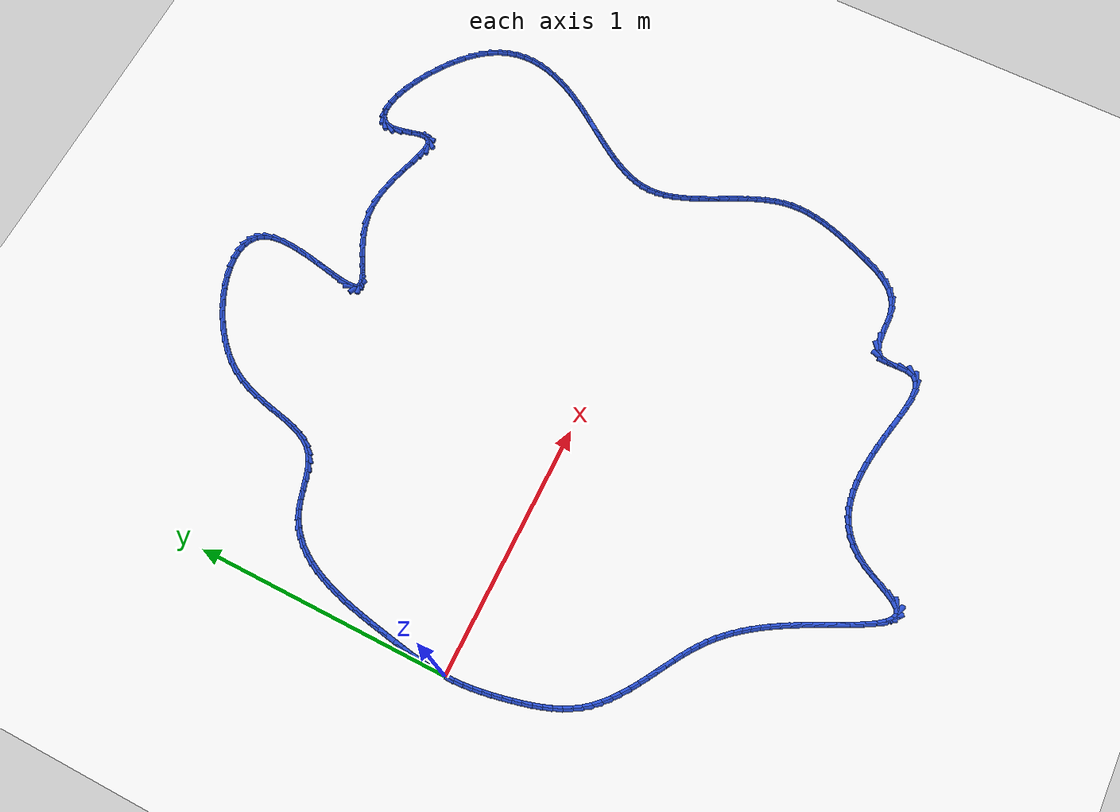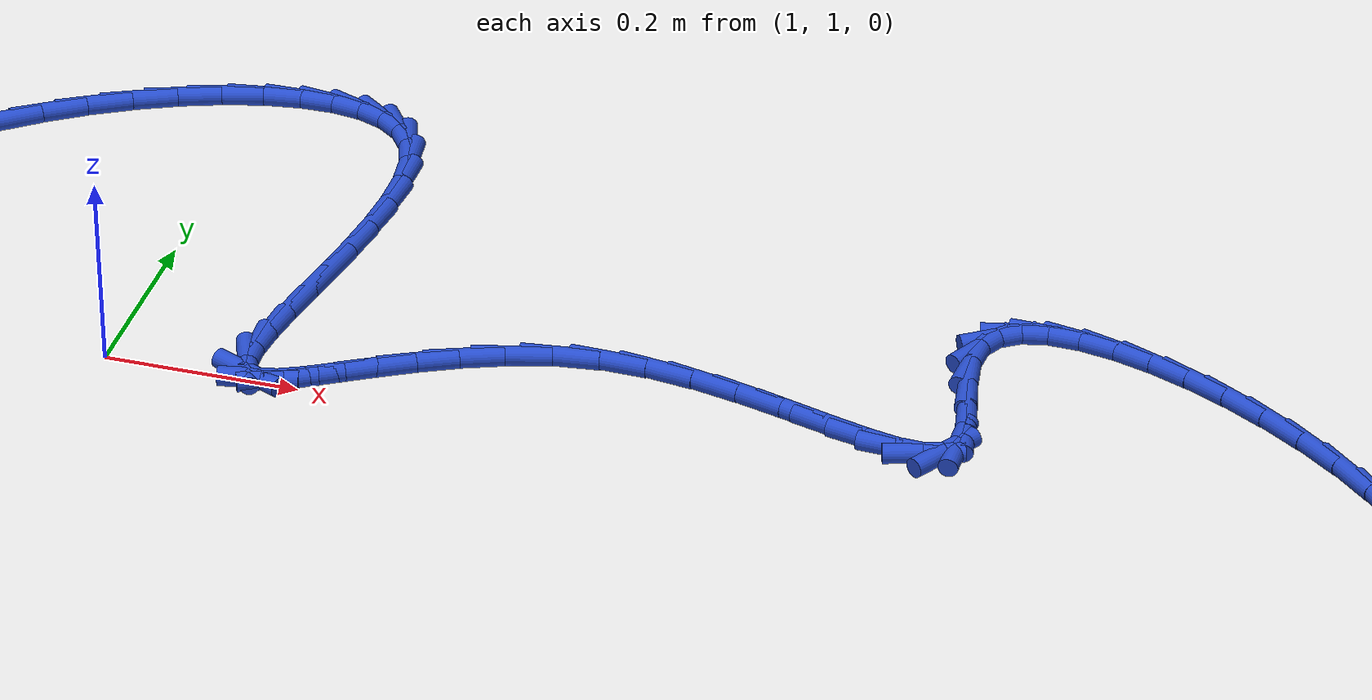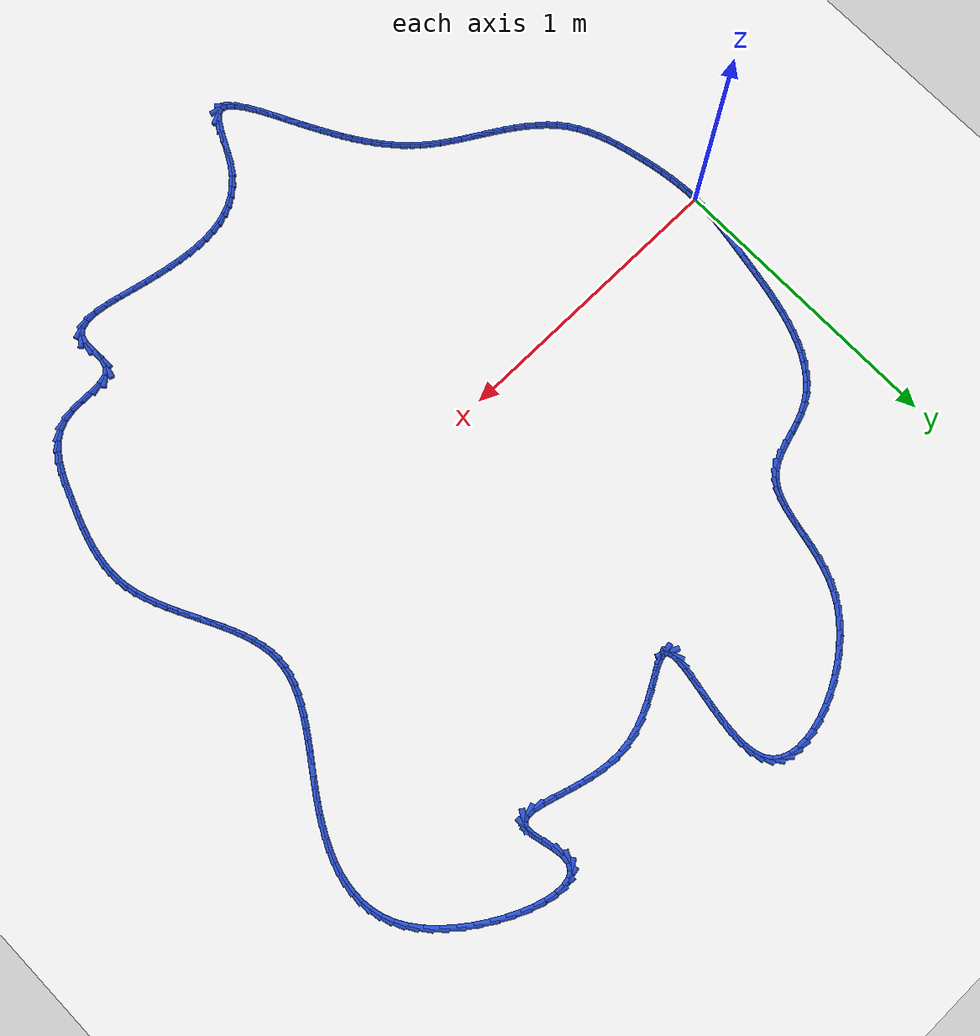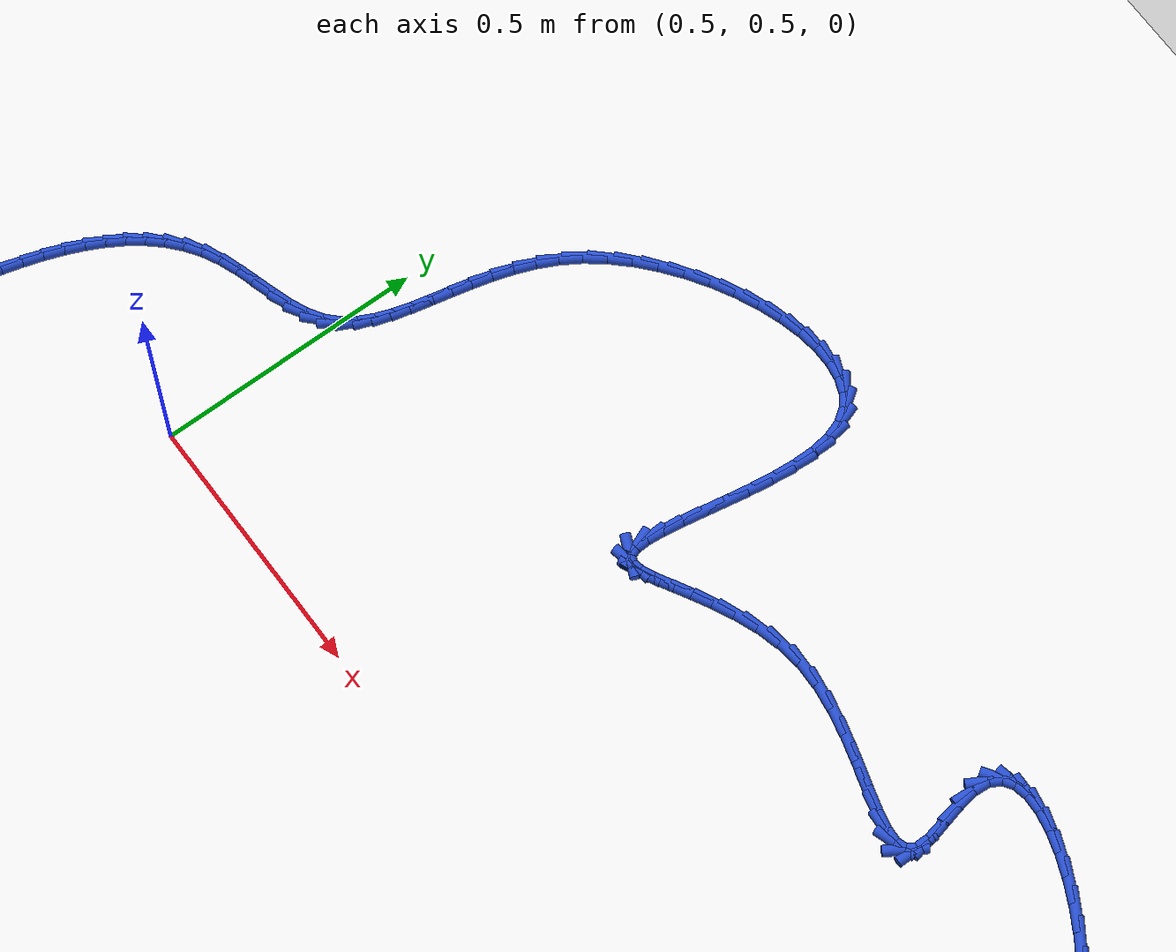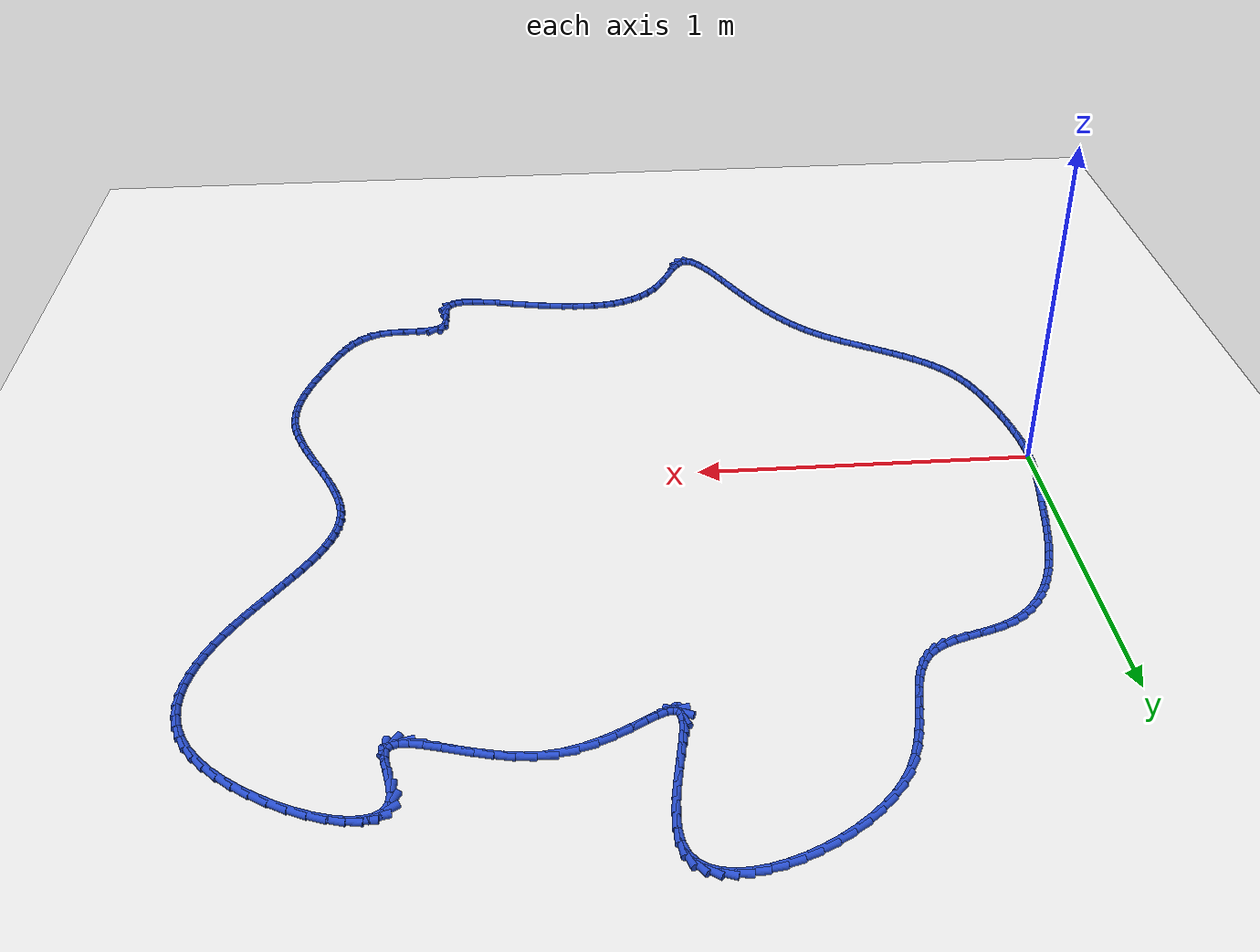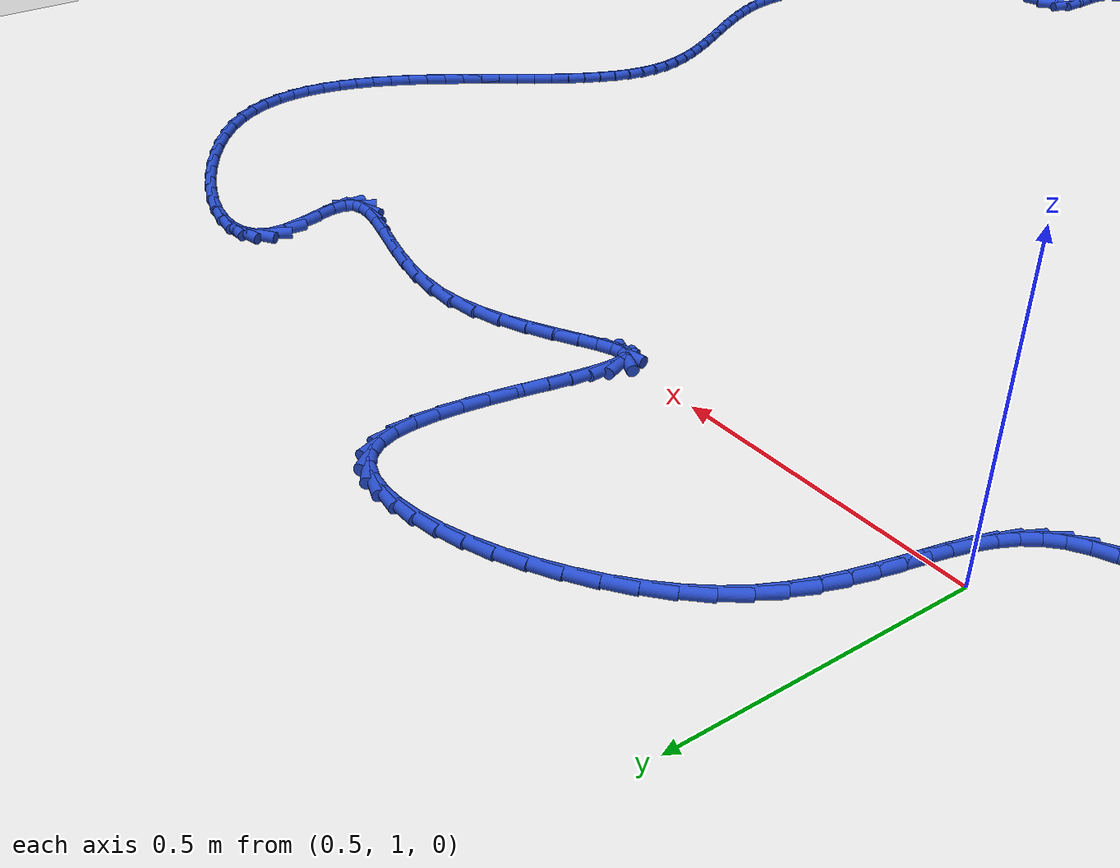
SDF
<sdf version="1.6">
 <world name="default">
  <light name="sun" type="directional">
   <pose>0 0 10 0 -0 0</pose>
   <diffuse>0.8 0.8 0.8 1</diffuse>
   <specular>0.2 0.2 0.2 1</specular>
   <attenuation>
    <range>1000</range>
    <constant>0.9</constant>
    <linear>0.01</linear>
    <quadratic>0.001</quadratic>
   </attenuation>
   <direction>-0.5 0.1 -0.9</direction>
  </light>
  <model name="ground_plane">
   <static>1</static>
   <link name="link">
    <collision name="collision">
     <geometry><plane><normal>0 0 1</normal><size>100 100</size></plane></geometry>
     <surface><friction><ode><mu>100</mu><mu2>50</mu2></ode></friction></surface>
    </collision>
    <visual name="visual">
     <cast_shadows>0</cast_shadows>
     <geometry><plane><normal>0 0 1</normal><size>100 100</size></plane></geometry>
     <material>
      <script><uri>file://media/materials/scripts/gazebo.material</uri><name>Gazebo/WhiteGlow</name></script>
     </material>
    </visual>
   </link>
  </model>
  <gravity>0 0 -9.8</gravity>
  <magnetic_field>6e-06 2.3e-05 -4.2e-05</magnetic_field>
  <atmosphere type="adiabatic"/>
  <physics name="default_physics" default="0" type="ode">
   <max_step_size>0.001</max_step_size>
   <real_time_factor>1</real_time_factor>
   <real_time_update_rate>1000</real_time_update_rate>
  </physics>
  <scene><ambient>0.4 0.4 0.4 1</ambient><background>0.7 0.7 0.7 1</background><shadows>1</shadows></scene>
  <spherical_coordinates>
   <surface_model>EARTH_WGS84</surface_model>
   <latitude_deg>0</latitude_deg>
   <longitude_deg>0</longitude_deg>
   <elevation>0</elevation>
   <heading_deg>0</heading_deg>
  </spherical_coordinates>
  <model name="line">
   <link name="link_0">
    <pose>-5.204170427930421e-18 -4.85722573273506e-17 0.01 0 1.57 1.5369050462411713</pose>
    <collision name="collision">
     <geometry><cylinder><radius>0.01</radius><length>0.08</length></cylinder></geometry>
    </collision>
    <visual name="visual">
     <material>
      <script><name>Gazebo/Blue</name><uri>file://media/materials/scripts/gazebo.material</uri></script>
     </material>
     <geometry><cylinder><radius>0.01</radius><length>0.08</length></cylinder></geometry>
    </visual>
   </link>
   <link name="link_1">
    <pose>0.001179614929062979 0.03479252576305422 0.01 0 1.57 1.4944790678501276</pose>
    <collision name="collision">
     <geometry><cylinder><radius>0.01</radius><length>0.08</length></cylinder></geometry>
    </collision>
    <visual name="visual">
     <material>
      <script><name>Gazebo/Blue</name><uri>file://media/materials/scripts/gazebo.material</uri></script>
     </material>
     <geometry><cylinder><radius>0.01</radius><length>0.08</length></cylinder></geometry>
    </visual>
   </link>
   <link name="link_2">
    <pose>0.0038353056540135727 0.06952297718088313 0.01 0 1.57 1.4592045873272361</pose>
    <collision name="collision">
     <geometry><cylinder><radius>0.01</radius><length>0.08</length></cylinder></geometry>
    </collision>
    <visual name="visual">
     <material>
      <script><name>Gazebo/Blue</name><uri>file://media/materials/scripts/gazebo.material</uri></script>
     </material>
     <geometry><cylinder><radius>0.01</radius><length>0.08</length></cylinder></geometry>
    </visual>
   </link>
   <link name="link_3">
    <pose>0.007736921789207115 0.10434103318704124 0.01 0 1.57 1.4314305865625976</pose>
    <collision name="collision">
     <geometry><cylinder><radius>0.01</radius><length>0.08</length></cylinder></geometry>
    </collision>
    <visual name="visual">
     <material>
      <script><name>Gazebo/Blue</name><uri>file://media/materials/scripts/gazebo.material</uri></script>
     </material>
     <geometry><cylinder><radius>0.01</radius><length>0.08</length></cylinder></geometry>
    </visual>
   </link>
   <link name="link_4">
    <pose>0.012654312948998951 0.13939637271508315 0.01 0 1.57 1.4112540431788643</pose>
    <collision name="collision">
     <geometry><cylinder><radius>0.01</radius><length>0.08</length></cylinder></geometry>
    </collision>
    <visual name="visual">
     <material>
      <script><name>Gazebo/Blue</name><uri>file://media/materials/scripts/gazebo.material</uri></script>
     </material>
     <geometry><cylinder><radius>0.01</radius><length>0.08</length></cylinder></geometry>
    </visual>
   </link>
   <link name="link_5">
    <pose>0.018357328747744418 0.17483867469856335 0.01 0 1.57 1.3985709128711143</pose>
    <collision name="collision">
     <geometry><cylinder><radius>0.01</radius><length>0.08</length></cylinder></geometry>
    </collision>
    <visual name="visual">
     <material>
      <script><name>Gazebo/Blue</name><uri>file://media/materials/scripts/gazebo.material</uri></script>
     </material>
     <geometry><cylinder><radius>0.01</radius><length>0.08</length></cylinder></geometry>
    </visual>
   </link>
   <link name="link_6">
    <pose>0.02461581879979885 0.21081761807103636 0.01 0 1.57 1.3931243501759252</pose>
    <collision name="collision">
     <geometry><cylinder><radius>0.01</radius><length>0.08</length></cylinder></geometry>
    </collision>
    <visual name="visual">
     <material>
      <script><name>Gazebo/Blue</name><uri>file://media/materials/scripts/gazebo.material</uri></script>
     </material>
     <geometry><cylinder><radius>0.01</radius><length>0.08</length></cylinder></geometry>
    </visual>
   </link>
   <link name="link_7">
    <pose>0.031199632719517586 0.2474828817660568 0.01 0 1.57 1.3925732620197482</pose>
    <collision name="collision">
     <geometry><cylinder><radius>0.01</radius><length>0.08</length></cylinder></geometry>
    </collision>
    <visual name="visual">
     <material>
      <script><name>Gazebo/Blue</name><uri>file://media/materials/scripts/gazebo.material</uri></script>
     </material>
     <geometry><cylinder><radius>0.01</radius><length>0.08</length></cylinder></geometry>
    </visual>
   </link>
   <link name="link_8">
    <pose>0.03794316011798658 0.28491898185479275 0.01 0 1.57 1.388079590155113</pose>
    <collision name="collision">
     <geometry><cylinder><radius>0.01</radius><length>0.08</length></cylinder></geometry>
    </collision>
    <visual name="visual">
     <material>
      <script><name>Gazebo/Blue</name><uri>file://media/materials/scripts/gazebo.material</uri></script>
     </material>
     <geometry><cylinder><radius>0.01</radius><length>0.08</length></cylinder></geometry>
    </visual>
   </link>
   <link name="link_9">
    <pose>0.0449654561309157 0.3229230216202673 0.01 0 1.57 1.3774066742535753</pose>
    <collision name="collision">
     <geometry><cylinder><radius>0.01</radius><length>0.08</length></cylinder></geometry>
    </collision>
    <visual name="visual">
     <material>
      <script><name>Gazebo/Blue</name><uri>file://media/materials/scripts/gazebo.material</uri></script>
     </material>
     <geometry><cylinder><radius>0.01</radius><length>0.08</length></cylinder></geometry>
    </visual>
   </link>
   <link name="link_10">
    <pose>0.052464035154047295 0.36121288788712996 0.01 0 1.57 1.3605367504029735</pose>
    <collision name="collision">
     <geometry><cylinder><radius>0.01</radius><length>0.08</length></cylinder></geometry>
    </collision>
    <visual name="visual">
     <material>
      <script><name>Gazebo/Blue</name><uri>file://media/materials/scripts/gazebo.material</uri></script>
     </material>
     <geometry><cylinder><radius>0.01</radius><length>0.08</length></cylinder></geometry>
    </visual>
   </link>
   <link name="link_11">
    <pose>0.06063641404318535 0.3995064649962271 0.01 0 1.57 1.3372407531217283</pose>
    <collision name="collision">
     <geometry><cylinder><radius>0.01</radius><length>0.08</length></cylinder></geometry>
    </collision>
    <visual name="visual">
     <material>
      <script><name>Gazebo/Blue</name><uri>file://media/materials/scripts/gazebo.material</uri></script>
     </material>
     <geometry><cylinder><radius>0.01</radius><length>0.08</length></cylinder></geometry>
    </visual>
   </link>
   <link name="link_12">
    <pose>0.06968010965413389 0.43752163728840493 0.01 0 1.57 1.3070901362691616</pose>
    <collision name="collision">
     <geometry><cylinder><radius>0.01</radius><length>0.08</length></cylinder></geometry>
    </collision>
    <visual name="visual">
     <material>
      <script><name>Gazebo/Blue</name><uri>file://media/materials/scripts/gazebo.material</uri></script>
     </material>
     <geometry><cylinder><radius>0.01</radius><length>0.08</length></cylinder></geometry>
    </visual>
   </link>
   <link name="link_13">
    <pose>0.07979263884269686 0.47497628910450973 0.01 0 1.57 1.2694643203815754</pose>
    <collision name="collision">
     <geometry><cylinder><radius>0.01</radius><length>0.08</length></cylinder></geometry>
    </collision>
    <visual name="visual">
     <material>
      <script><name>Gazebo/Blue</name><uri>file://media/materials/scripts/gazebo.material</uri></script>
     </material>
     <geometry><cylinder><radius>0.01</radius><length>0.08</length></cylinder></geometry>
    </visual>
   </link>
   <link name="link_14">
    <pose>0.09117151846467822 0.5115883047853877 0.01 0 1.57 1.2235620936816765</pose>
    <collision name="collision">
     <geometry><cylinder><radius>0.01</radius><length>0.08</length></cylinder></geometry>
    </collision>
    <visual name="visual">
     <material>
      <script><name>Gazebo/Blue</name><uri>file://media/materials/scripts/gazebo.material</uri></script>
     </material>
     <geometry><cylinder><radius>0.01</radius><length>0.08</length></cylinder></geometry>
    </visual>
   </link>
   <link name="link_15">
    <pose>0.10401426537588201 0.5470755686718852 0.01 0 1.57 1.1684296489621728</pose>
    <collision name="collision">
     <geometry><cylinder><radius>0.01</radius><length>0.08</length></cylinder></geometry>
    </collision>
    <visual name="visual">
     <material>
      <script><name>Gazebo/Blue</name><uri>file://media/materials/scripts/gazebo.material</uri></script>
     </material>
     <geometry><cylinder><radius>0.01</radius><length>0.08</length></cylinder></geometry>
    </visual>
   </link>
   <link name="link_16">
    <pose>0.1185183964321122 0.5811559651048483 0.01 0 1.57 1.1030246761978932</pose>
    <collision name="collision">
     <geometry><cylinder><radius>0.01</radius><length>0.08</length></cylinder></geometry>
    </collision>
    <visual name="visual">
     <material>
      <script><name>Gazebo/Blue</name><uri>file://media/materials/scripts/gazebo.material</uri></script>
     </material>
     <geometry><cylinder><radius>0.01</radius><length>0.08</length></cylinder></geometry>
    </visual>
   </link>
   <link name="link_17">
    <pose>0.1348814284891728 0.6135473784251237 0.01 0 1.57 1.0263437357575256</pose>
    <collision name="collision">
     <geometry><cylinder><radius>0.01</radius><length>0.08</length></cylinder></geometry>
    </collision>
    <visual name="visual">
     <material>
      <script><name>Gazebo/Blue</name><uri>file://media/materials/scripts/gazebo.material</uri></script>
     </material>
     <geometry><cylinder><radius>0.01</radius><length>0.08</length></cylinder></geometry>
    </visual>
   </link>
   <link name="link_18">
    <pose>0.1533008784028677 0.643967692973557 0.01 0 1.57 0.9376433334057122</pose>
    <collision name="collision">
     <geometry><cylinder><radius>0.01</radius><length>0.08</length></cylinder></geometry>
    </collision>
    <visual name="visual">
     <material>
      <script><name>Gazebo/Blue</name><uri>file://media/materials/scripts/gazebo.material</uri></script>
     </material>
     <geometry><cylinder><radius>0.01</radius><length>0.08</length></cylinder></geometry>
    </visual>
   </link>
   <link name="link_19">
    <pose>0.173974263029001 0.6721347930909952 0.01 0 1.57 0.8367702398681535</pose>
    <collision name="collision">
     <geometry><cylinder><radius>0.01</radius><length>0.08</length></cylinder></geometry>
    </collision>
    <visual name="visual">
     <material>
      <script><name>Gazebo/Blue</name><uri>file://media/materials/scripts/gazebo.material</uri></script>
     </material>
     <geometry><cylinder><radius>0.01</radius><length>0.08</length></cylinder></geometry>
    </visual>
   </link>
   <link name="link_20">
    <pose>0.19709909922337657 0.6977665631182838 0.01 0 1.57 0.7245637853239802</pose>
    <collision name="collision">
     <geometry><cylinder><radius>0.01</radius><length>0.08</length></cylinder></geometry>
    </collision>
    <visual name="visual">
     <material>
      <script><name>Gazebo/Blue</name><uri>file://media/materials/scripts/gazebo.material</uri></script>
     </material>
     <geometry><cylinder><radius>0.01</radius><length>0.08</length></cylinder></geometry>
    </visual>
   </link>
   <link name="link_21">
    <pose>0.2228729038417985 0.7205808873962697 0.01 0 1.57 0.6031958058943186</pose>
    <collision name="collision">
     <geometry><cylinder><radius>0.01</radius><length>0.08</length></cylinder></geometry>
    </collision>
    <visual name="visual">
     <material>
      <script><name>Gazebo/Blue</name><uri>file://media/materials/scripts/gazebo.material</uri></script>
     </material>
     <geometry><cylinder><radius>0.01</radius><length>0.08</length></cylinder></geometry>
    </visual>
   </link>
   <link name="link_22">
    <pose>0.25149319374007073 0.7402956502657989 0.01 0 1.57 0.4764705233320054</pose>
    <collision name="collision">
     <geometry><cylinder><radius>0.01</radius><length>0.08</length></cylinder></geometry>
    </collision>
    <visual name="visual">
     <material>
      <script><name>Gazebo/Blue</name><uri>file://media/materials/scripts/gazebo.material</uri></script>
     </material>
     <geometry><cylinder><radius>0.01</radius><length>0.08</length></cylinder></geometry>
    </visual>
   </link>
   <link name="link_23">
    <pose>0.28315084577020794 0.7566352080083728 0.01 0 1.57 0.36785588193311014</pose>
    <collision name="collision">
     <geometry><cylinder><radius>0.01</radius><length>0.08</length></cylinder></geometry>
    </collision>
    <visual name="visual">
     <material>
      <script><name>Gazebo/Blue</name><uri>file://media/materials/scripts/gazebo.material</uri></script>
     </material>
     <geometry><cylinder><radius>0.01</radius><length>0.08</length></cylinder></geometry>
    </visual>
   </link>
   <link name="link_24">
    <pose>0.3174806974591322 0.7698658824868287 0.01 0 1.57 0.3075824316335672</pose>
    <collision name="collision">
     <geometry><cylinder><radius>0.01</radius><length>0.08</length></cylinder></geometry>
    </collision>
    <visual name="visual">
     <material>
      <script><name>Gazebo/Blue</name><uri>file://media/materials/scripts/gazebo.material</uri></script>
     </material>
     <geometry><cylinder><radius>0.01</radius><length>0.08</length></cylinder></geometry>
    </visual>
   </link>
   <link name="link_25">
    <pose>0.3531502772942382 0.7811968213360009 0.01 0 1.57 0.29302371395674015</pose>
    <collision name="collision">
     <geometry><cylinder><radius>0.01</radius><length>0.08</length></cylinder></geometry>
    </collision>
    <visual name="visual">
     <material>
      <script><name>Gazebo/Blue</name><uri>file://media/materials/scripts/gazebo.material</uri></script>
     </material>
     <geometry><cylinder><radius>0.01</radius><length>0.08</length></cylinder></geometry>
    </visual>
   </link>
   <link name="link_26">
    <pose>0.3887302295905153 0.7919316041570427 0.01 0 1.57 0.32408850256056776</pose>
    <collision name="collision">
     <geometry><cylinder><radius>0.01</radius><length>0.08</length></cylinder></geometry>
    </collision>
    <visual name="visual">
     <material>
      <script><name>Gazebo/Blue</name><uri>file://media/materials/scripts/gazebo.material</uri></script>
     </material>
     <geometry><cylinder><radius>0.01</radius><length>0.08</length></cylinder></geometry>
    </visual>
   </link>
   <link name="link_27">
    <pose>0.42279119866295295 0.803373810551108 0.01 0 1.57 0.40812471255408317</pose>
    <collision name="collision">
     <geometry><cylinder><radius>0.01</radius><length>0.08</length></cylinder></geometry>
    </collision>
    <visual name="visual">
     <material>
      <script><name>Gazebo/Blue</name><uri>file://media/materials/scripts/gazebo.material</uri></script>
     </material>
     <geometry><cylinder><radius>0.01</radius><length>0.08</length></cylinder></geometry>
    </visual>
   </link>
   <link name="link_28">
    <pose>0.45390382882654096 0.8168270201193508 0.01 0 1.57 0.5597559717216742</pose>
    <collision name="collision">
     <geometry><cylinder><radius>0.01</radius><length>0.08</length></cylinder></geometry>
    </collision>
    <visual name="visual">
     <material>
      <script><name>Gazebo/Blue</name><uri>file://media/materials/scripts/gazebo.material</uri></script>
     </material>
     <geometry><cylinder><radius>0.01</radius><length>0.08</length></cylinder></geometry>
    </visual>
   </link>
   <link name="link_29">
    <pose>0.4806497685451893 0.8335862837677136 0.01 0 1.57 0.7617756545515256</pose>
    <collision name="collision">
     <geometry><cylinder><radius>0.01</radius><length>0.08</length></cylinder></geometry>
    </collision>
    <visual name="visual">
     <material>
      <script><name>Gazebo/Blue</name><uri>file://media/materials/scripts/gazebo.material</uri></script>
     </material>
     <geometry><cylinder><radius>0.01</radius><length>0.08</length></cylinder></geometry>
    </visual>
   </link>
   <link name="link_30">
    <pose>0.5024014041411227 0.8543337960845812 0.01 0 1.57 0.9504129710283877</pose>
    <collision name="collision">
     <geometry><cylinder><radius>0.01</radius><length>0.08</length></cylinder></geometry>
    </collision>
    <visual name="visual">
     <material>
      <script><name>Gazebo/Blue</name><uri>file://media/materials/scripts/gazebo.material</uri></script>
     </material>
     <geometry><cylinder><radius>0.01</radius><length>0.08</length></cylinder></geometry>
    </visual>
   </link>
   <link name="link_31">
    <pose>0.5198383411708368 0.8787385997550478 0.01 0 1.57 1.104075658613848</pose>
    <collision name="collision">
     <geometry><cylinder><radius>0.01</radius><length>0.08</length></cylinder></geometry>
    </collision>
    <visual name="visual">
     <material>
      <script><name>Gazebo/Blue</name><uri>file://media/materials/scripts/gazebo.material</uri></script>
     </material>
     <geometry><cylinder><radius>0.01</radius><length>0.08</length></cylinder></geometry>
    </visual>
   </link>
   <link name="link_32">
    <pose>0.5337627403474583 0.9063747518742298 0.01 0 1.57 1.2178432131364294</pose>
    <collision name="collision">
     <geometry><cylinder><radius>0.01</radius><length>0.08</length></cylinder></geometry>
    </collision>
    <visual name="visual">
     <material>
      <script><name>Gazebo/Blue</name><uri>file://media/materials/scripts/gazebo.material</uri></script>
     </material>
     <geometry><cylinder><radius>0.01</radius><length>0.08</length></cylinder></geometry>
    </visual>
   </link>
   <link name="link_33">
    <pose>0.5449767623841129 0.9368163095372418 0.01 0 1.57 1.2945155241710844</pose>
    <collision name="collision">
     <geometry><cylinder><radius>0.01</radius><length>0.08</length></cylinder></geometry>
    </collision>
    <visual name="visual">
     <material>
      <script><name>Gazebo/Blue</name><uri>file://media/materials/scripts/gazebo.material</uri></script>
     </material>
     <geometry><cylinder><radius>0.01</radius><length>0.08</length></cylinder></geometry>
    </visual>
   </link>
   <link name="link_34">
    <pose>0.554282567993927 0.9696373298392008 0.01 0 1.57 1.339228729796562</pose>
    <collision name="collision">
     <geometry><cylinder><radius>0.01</radius><length>0.08</length></cylinder></geometry>
    </collision>
    <visual name="visual">
     <material>
      <script><name>Gazebo/Blue</name><uri>file://media/materials/scripts/gazebo.material</uri></script>
     </material>
     <geometry><cylinder><radius>0.01</radius><length>0.08</length></cylinder></geometry>
    </visual>
   </link>
   <link name="link_35">
    <pose>0.5624823178900267 1.0044118698752216 0.01 0 1.57 1.3566280548710765</pose>
    <collision name="collision">
     <geometry><cylinder><radius>0.01</radius><length>0.08</length></cylinder></geometry>
    </collision>
    <visual name="visual">
     <material>
      <script><name>Gazebo/Blue</name><uri>file://media/materials/scripts/gazebo.material</uri></script>
     </material>
     <geometry><cylinder><radius>0.01</radius><length>0.08</length></cylinder></geometry>
    </visual>
   </link>
   <link name="link_36">
    <pose>0.5703781727855383 1.0407139867404205 0.01 0 1.57 1.3500347471364218</pose>
    <collision name="collision">
     <geometry><cylinder><radius>0.01</radius><length>0.08</length></cylinder></geometry>
    </collision>
    <visual name="visual">
     <material>
      <script><name>Gazebo/Blue</name><uri>file://media/materials/scripts/gazebo.material</uri></script>
     </material>
     <geometry><cylinder><radius>0.01</radius><length>0.08</length></cylinder></geometry>
    </visual>
   </link>
   <link name="link_37">
    <pose>0.5787722933935876 1.0781177375299127 0.01 0 1.57 1.3215047693264759</pose>
    <collision name="collision">
     <geometry><cylinder><radius>0.01</radius><length>0.08</length></cylinder></geometry>
    </collision>
    <visual name="visual">
     <material>
      <script><name>Gazebo/Blue</name><uri>file://media/materials/scripts/gazebo.material</uri></script>
     </material>
     <geometry><cylinder><radius>0.01</radius><length>0.08</length></cylinder></geometry>
    </visual>
   </link>
   <link name="link_38">
    <pose>0.5884668404273015 1.1161971793388146 0.01 0 1.57 1.2722130922830535</pose>
    <collision name="collision">
     <geometry><cylinder><radius>0.01</radius><length>0.08</length></cylinder></geometry>
    </collision>
    <visual name="visual">
     <material>
      <script><name>Gazebo/Blue</name><uri>file://media/materials/scripts/gazebo.material</uri></script>
     </material>
     <geometry><cylinder><radius>0.01</radius><length>0.08</length></cylinder></geometry>
    </visual>
   </link>
   <link name="link_39">
    <pose>0.6002639745998056 1.1545263692622418 0.01 0 1.57 1.2029912521550543</pose>
    <collision name="collision">
     <geometry><cylinder><radius>0.01</radius><length>0.08</length></cylinder></geometry>
    </collision>
    <visual name="visual">
     <material>
      <script><name>Gazebo/Blue</name><uri>file://media/materials/scripts/gazebo.material</uri></script>
     </material>
     <geometry><cylinder><radius>0.01</radius><length>0.08</length></cylinder></geometry>
    </visual>
   </link>
   <link name="link_40">
    <pose>0.6149658566242262 1.1926793643953097 0.01 0 1.57 1.1149902028308967</pose>
    <collision name="collision">
     <geometry><cylinder><radius>0.01</radius><length>0.08</length></cylinder></geometry>
    </collision>
    <visual name="visual">
     <material>
      <script><name>Gazebo/Blue</name><uri>file://media/materials/scripts/gazebo.material</uri></script>
     </material>
     <geometry><cylinder><radius>0.01</radius><length>0.08</length></cylinder></geometry>
    </visual>
   </link>
   <link name="link_41">
    <pose>0.6333746472136897 1.2302302218331345 0.01 0 1.57 1.0104270688908756</pose>
    <collision name="collision">
     <geometry><cylinder><radius>0.01</radius><length>0.08</length></cylinder></geometry>
    </collision>
    <visual name="visual">
     <material>
      <script><name>Gazebo/Blue</name><uri>file://media/materials/scripts/gazebo.material</uri></script>
     </material>
     <geometry><cylinder><radius>0.01</radius><length>0.08</length></cylinder></geometry>
    </visual>
   </link>
   <link name="link_42">
    <pose>0.6562914018405819 1.2667530384862449 0.01 0 1.57 0.9004035265437024</pose>
    <collision name="collision">
     <geometry><cylinder><radius>0.01</radius><length>0.08</length></cylinder></geometry>
    </collision>
    <visual name="visual">
     <material>
      <script><name>Gazebo/Blue</name><uri>file://media/materials/scripts/gazebo.material</uri></script>
     </material>
     <geometry><cylinder><radius>0.01</radius><length>0.08</length></cylinder></geometry>
    </visual>
   </link>
   <link name="link_43">
    <pose>0.6841089511659812 1.3018366172374258 0.01 0 1.57 0.8033685839622964</pose>
    <collision name="collision">
     <geometry><cylinder><radius>0.01</radius><length>0.08</length></cylinder></geometry>
    </collision>
    <visual name="visual">
     <material>
      <script><name>Gazebo/Blue</name><uri>file://media/materials/scripts/gazebo.material</uri></script>
     </material>
     <geometry><cylinder><radius>0.01</radius><length>0.08</length></cylinder></geometry>
    </visual>
   </link>
   <link name="link_44">
    <pose>0.7162039436599458 1.3351063681199664 0.01 0 1.57 0.7179146089818566</pose>
    <collision name="collision">
     <geometry><cylinder><radius>0.01</radius><length>0.08</length></cylinder></geometry>
    </collision>
    <visual name="visual">
     <material>
      <script><name>Gazebo/Blue</name><uri>file://media/materials/scripts/gazebo.material</uri></script>
     </material>
     <geometry><cylinder><radius>0.01</radius><length>0.08</length></cylinder></geometry>
    </visual>
   </link>
   <link name="link_45">
    <pose>0.7517975611359362 1.3661933017290904 0.01 0 1.57 0.6401528496057675</pose>
    <collision name="collision">
     <geometry><cylinder><radius>0.01</radius><length>0.08</length></cylinder></geometry>
    </collision>
    <visual name="visual">
     <material>
      <script><name>Gazebo/Blue</name><uri>file://media/materials/scripts/gazebo.material</uri></script>
     </material>
     <geometry><cylinder><radius>0.01</radius><length>0.08</length></cylinder></geometry>
    </visual>
   </link>
   <link name="link_46">
    <pose>0.7901109854074131 1.3947284286600203 0.01 0 1.57 0.5666918426993591</pose>
    <collision name="collision">
     <geometry><cylinder><radius>0.01</radius><length>0.08</length></cylinder></geometry>
    </collision>
    <visual name="visual">
     <material>
      <script><name>Gazebo/Blue</name><uri>file://media/materials/scripts/gazebo.material</uri></script>
     </material>
     <geometry><cylinder><radius>0.01</radius><length>0.08</length></cylinder></geometry>
    </visual>
   </link>
   <link name="link_47">
    <pose>0.8303653982878372 1.4203427595079796 0.01 0 1.57 0.49437754574316994</pose>
    <collision name="collision">
     <geometry><cylinder><radius>0.01</radius><length>0.08</length></cylinder></geometry>
    </collision>
    <visual name="visual">
     <material>
      <script><name>Gazebo/Blue</name><uri>file://media/materials/scripts/gazebo.material</uri></script>
     </material>
     <geometry><cylinder><radius>0.01</radius><length>0.08</length></cylinder></geometry>
    </visual>
   </link>
   <link name="link_48">
    <pose>0.871781981590669 1.4426673048681917 0.01 0 1.57 0.41998138685529285</pose>
    <collision name="collision">
     <geometry><cylinder><radius>0.01</radius><length>0.08</length></cylinder></geometry>
    </collision>
    <visual name="visual">
     <material>
      <script><name>Gazebo/Blue</name><uri>file://media/materials/scripts/gazebo.material</uri></script>
     </material>
     <geometry><cylinder><radius>0.01</radius><length>0.08</length></cylinder></geometry>
    </visual>
   </link>
   <link name="link_49">
    <pose>0.9135819171293686 1.4613330753358784 0.01 0 1.57 0.33982221556580244</pose>
    <collision name="collision">
     <geometry><cylinder><radius>0.01</radius><length>0.08</length></cylinder></geometry>
    </collision>
    <visual name="visual">
     <material>
      <script><name>Gazebo/Blue</name><uri>file://media/materials/scripts/gazebo.material</uri></script>
     </material>
     <geometry><cylinder><radius>0.01</radius><length>0.08</length></cylinder></geometry>
    </visual>
   </link>
   <link name="link_50">
    <pose>0.9549863867173972 1.475971081506264 0.01 0 1.57 0.24927178854312962</pose>
    <collision name="collision">
     <geometry><cylinder><radius>0.01</radius><length>0.08</length></cylinder></geometry>
    </collision>
    <visual name="visual">
     <material>
      <script><name>Gazebo/Blue</name><uri>file://media/materials/scripts/gazebo.material</uri></script>
     </material>
     <geometry><cylinder><radius>0.01</radius><length>0.08</length></cylinder></geometry>
    </visual>
   </link>
   <link name="link_51">
    <pose>0.995216572168215 1.486212333974571 0.01 0 1.57 0.14208534853576427</pose>
    <collision name="collision">
     <geometry><cylinder><radius>0.01</radius><length>0.08</length></cylinder></geometry>
    </collision>
    <visual name="visual">
     <material>
      <script><name>Gazebo/Blue</name><uri>file://media/materials/scripts/gazebo.material</uri></script>
     </material>
     <geometry><cylinder><radius>0.01</radius><length>0.08</length></cylinder></geometry>
    </visual>
   </link>
   <link name="link_52">
    <pose>1.0334936552952834 1.4916878433360234 0.01 0 1.57 0.00958685752569644</pose>
    <collision name="collision">
     <geometry><cylinder><radius>0.01</radius><length>0.08</length></cylinder></geometry>
    </collision>
    <visual name="visual">
     <material>
      <script><name>Gazebo/Blue</name><uri>file://media/materials/scripts/gazebo.material</uri></script>
     </material>
     <geometry><cylinder><radius>0.01</radius><length>0.08</length></cylinder></geometry>
    </visual>
   </link>
   <link name="link_53">
    <pose>1.0690388179120616 1.4920286201858433 0.01 0 1.57 -0.15979453970036117</pose>
    <collision name="collision">
     <geometry><cylinder><radius>0.01</radius><length>0.08</length></cylinder></geometry>
    </collision>
    <visual name="visual">
     <material>
      <script><name>Gazebo/Blue</name><uri>file://media/materials/scripts/gazebo.material</uri></script>
     </material>
     <geometry><cylinder><radius>0.01</radius><length>0.08</length></cylinder></geometry>
    </visual>
   </link>
   <link name="link_54">
    <pose>1.1010732418320113 1.4868656751192542 0.01 0 1.57 -0.3785694357290226</pose>
    <collision name="collision">
     <geometry><cylinder><radius>0.01</radius><length>0.08</length></cylinder></geometry>
    </collision>
    <visual name="visual">
     <material>
      <script><name>Gazebo/Blue</name><uri>file://media/materials/scripts/gazebo.material</uri></script>
     </material>
     <geometry><cylinder><radius>0.01</radius><length>0.08</length></cylinder></geometry>
    </visual>
   </link>
   <link name="link_55">
    <pose>1.1288181088685927 1.4758300187314792 0.01 0 1.57 -0.6510775557322538</pose>
    <collision name="collision">
     <geometry><cylinder><radius>0.01</radius><length>0.08</length></cylinder></geometry>
    </collision>
    <visual name="visual">
     <material>
      <script><name>Gazebo/Blue</name><uri>file://media/materials/scripts/gazebo.material</uri></script>
     </material>
     <geometry><cylinder><radius>0.01</radius><length>0.08</length></cylinder></geometry>
    </visual>
   </link>
   <link name="link_56">
    <pose>1.1514946008352664 1.4585526616177409 0.01 0 1.57 -0.9570518687198416</pose>
    <collision name="collision">
     <geometry><cylinder><radius>0.01</radius><length>0.08</length></cylinder></geometry>
    </collision>
    <visual name="visual">
     <material>
      <script><name>Gazebo/Blue</name><uri>file://media/materials/scripts/gazebo.material</uri></script>
     </material>
     <geometry><cylinder><radius>0.01</radius><length>0.08</length></cylinder></geometry>
    </visual>
   </link>
   <link name="link_57">
    <pose>1.1683238995454932 1.4346646143732629 0.01 0 1.57 -1.2436300506748685</pose>
    <collision name="collision">
     <geometry><cylinder><radius>0.01</radius><length>0.08</length></cylinder></geometry>
    </collision>
    <visual name="visual">
     <material>
      <script><name>Gazebo/Blue</name><uri>file://media/materials/scripts/gazebo.material</uri></script>
     </material>
     <geometry><cylinder><radius>0.01</radius><length>0.08</length></cylinder></geometry>
    </visual>
   </link>
   <link name="link_58">
    <pose>1.1787318026879587 1.4039955618378783 0.01 0 1.57 -1.444637079950514</pose>
    <collision name="collision">
     <geometry><cylinder><radius>0.01</radius><length>0.08</length></cylinder></geometry>
    </collision>
    <visual name="visual">
     <material>
      <script><name>Gazebo/Blue</name><uri>file://media/materials/scripts/gazebo.material</uri></script>
     </material>
     <geometry><cylinder><radius>0.01</radius><length>0.08</length></cylinder></geometry>
    </visual>
   </link>
   <link name="link_59">
    <pose>1.1833542707400957 1.3675502109636808 0.01 0 1.57 1.5687435442339484</pose>
    <collision name="collision">
     <geometry><cylinder><radius>0.01</radius><length>0.08</length></cylinder></geometry>
    </collision>
    <visual name="visual">
     <material>
      <script><name>Gazebo/Blue</name><uri>file://media/materials/scripts/gazebo.material</uri></script>
     </material>
     <geometry><cylinder><radius>0.01</radius><length>0.08</length></cylinder></geometry>
    </visual>
   </link>
   <link name="link_60">
    <pose>1.1832705447374465 1.3267636772912266 0.01 0 1.57 1.4860865900125153</pose>
    <collision name="collision">
     <geometry><cylinder><radius>0.01</radius><length>0.08</length></cylinder></geometry>
    </collision>
    <visual name="visual">
     <material>
      <script><name>Gazebo/Blue</name><uri>file://media/materials/scripts/gazebo.material</uri></script>
     </material>
     <geometry><cylinder><radius>0.01</radius><length>0.08</length></cylinder></geometry>
    </visual>
   </link>
   <link name="link_61">
    <pose>1.1795605325885823 1.2830717238694571 0.01 0 1.57 1.433139103271464</pose>
    <collision name="collision">
     <geometry><cylinder><radius>0.01</radius><length>0.08</length></cylinder></geometry>
    </collision>
    <visual name="visual">
     <material>
      <script><name>Gazebo/Blue</name><uri>file://media/materials/scripts/gazebo.material</uri></script>
     </material>
     <geometry><cylinder><radius>0.01</radius><length>0.08</length></cylinder></geometry>
    </visual>
   </link>
   <link name="link_62">
    <pose>1.1733041422020754 1.237910113747317 0.01 0 1.57 1.4015541714508555</pose>
    <collision name="collision">
     <geometry><cylinder><radius>0.01</radius><length>0.08</length></cylinder></geometry>
    </collision>
    <visual name="visual">
     <material>
      <script><name>Gazebo/Blue</name><uri>file://media/materials/scripts/gazebo.material</uri></script>
     </material>
     <geometry><cylinder><radius>0.01</radius><length>0.08</length></cylinder></geometry>
    </visual>
   </link>
   <link name="link_63">
    <pose>1.165581281486497 1.1927146099737485 0.01 0 1.57 1.3876967503209767</pose>
    <collision name="collision">
     <geometry><cylinder><radius>0.01</radius><length>0.08</length></cylinder></geometry>
    </collision>
    <visual name="visual">
     <material>
      <script><name>Gazebo/Blue</name><uri>file://media/materials/scripts/gazebo.material</uri></script>
     </material>
     <geometry><cylinder><radius>0.01</radius><length>0.08</length></cylinder></geometry>
    </visual>
   </link>
   <link name="link_64">
    <pose>1.157471858350418 1.1489209755976948 0.01 0 1.57 1.3916630397164247</pose>
    <collision name="collision">
     <geometry><cylinder><radius>0.01</radius><length>0.08</length></cylinder></geometry>
    </collision>
    <visual name="visual">
     <material>
      <script><name>Gazebo/Blue</name><uri>file://media/materials/scripts/gazebo.material</uri></script>
     </material>
     <geometry><cylinder><radius>0.01</radius><length>0.08</length></cylinder></geometry>
    </visual>
   </link>
   <link name="link_65">
    <pose>1.1500557807024114 1.1079649736680994 0.01 0 1.57 1.4181644058250906</pose>
    <collision name="collision">
     <geometry><cylinder><radius>0.01</radius><length>0.08</length></cylinder></geometry>
    </collision>
    <visual name="visual">
     <material>
      <script><name>Gazebo/Blue</name><uri>file://media/materials/scripts/gazebo.material</uri></script>
     </material>
     <geometry><cylinder><radius>0.01</radius><length>0.08</length></cylinder></geometry>
    </visual>
   </link>
   <link name="link_66">
    <pose>1.1444129564510483 1.071282367233905 0.01 0 1.57 1.4809724146458034</pose>
    <collision name="collision">
     <geometry><cylinder><radius>0.01</radius><length>0.08</length></cylinder></geometry>
    </collision>
    <visual name="visual">
     <material>
      <script><name>Gazebo/Blue</name><uri>file://media/materials/scripts/gazebo.material</uri></script>
     </material>
     <geometry><cylinder><radius>0.01</radius><length>0.08</length></cylinder></geometry>
    </visual>
   </link>
   <link name="link_67">
    <pose>1.1416232935048996 1.0403089193440542 0.01 0 1.57 -1.522848338526374</pose>
    <collision name="collision">
     <geometry><cylinder><radius>0.01</radius><length>0.08</length></cylinder></geometry>
    </collision>
    <visual name="visual">
     <material>
      <script><name>Gazebo/Blue</name><uri>file://media/materials/scripts/gazebo.material</uri></script>
     </material>
     <geometry><cylinder><radius>0.01</radius><length>0.08</length></cylinder></geometry>
    </visual>
   </link>
   <link name="link_68">
    <pose>1.142766699772538 1.0164803930474915 0.01 0 1.57 -1.1870575808474761</pose>
    <collision name="collision">
     <geometry><cylinder><radius>0.01</radius><length>0.08</length></cylinder></geometry>
    </collision>
    <visual name="visual">
     <material>
      <script><name>Gazebo/Blue</name><uri>file://media/materials/scripts/gazebo.material</uri></script>
     </material>
     <geometry><cylinder><radius>0.01</radius><length>0.08</length></cylinder></geometry>
    </visual>
   </link>
   <link name="link_69">
    <pose>1.1489230831625346 1.0012325513931586 0.01 0 1.57 -0.42190029770812376</pose>
    <collision name="collision">
     <geometry><cylinder><radius>0.01</radius><length>0.08</length></cylinder></geometry>
    </collision>
    <visual name="visual">
     <material>
      <script><name>Gazebo/Blue</name><uri>file://media/materials/scripts/gazebo.material</uri></script>
     </material>
     <geometry><cylinder><radius>0.01</radius><length>0.08</length></cylinder></geometry>
    </visual>
   </link>
   <link name="link_70">
    <pose>1.1610688202278772 0.9957808917240109 0.01 0 1.57 0.19157201070864585</pose>
    <collision name="collision">
     <geometry><cylinder><radius>0.01</radius><length>0.08</length></cylinder></geometry>
    </collision>
    <visual name="visual">
     <material>
      <script><name>Gazebo/Blue</name><uri>file://media/materials/scripts/gazebo.material</uri></script>
     </material>
     <geometry><cylinder><radius>0.01</radius><length>0.08</length></cylinder></geometry>
    </visual>
   </link>
   <link name="link_71">
    <pose>1.1792217830529335 0.9993016676941432 0.01 0 1.57 0.41999487995042717</pose>
    <collision name="collision">
     <geometry><cylinder><radius>0.01</radius><length>0.08</length></cylinder></geometry>
    </collision>
    <visual name="visual">
     <material>
      <script><name>Gazebo/Blue</name><uri>file://media/materials/scripts/gazebo.material</uri></script>
     </material>
     <geometry><cylinder><radius>0.01</radius><length>0.08</length></cylinder></geometry>
    </visual>
   </link>
   <link name="link_72">
    <pose>1.2028808810101816 1.0098670260185412 0.01 0 1.57 0.5003953882442692</pose>
    <collision name="collision">
     <geometry><cylinder><radius>0.01</radius><length>0.08</length></cylinder></geometry>
    </collision>
    <visual name="visual">
     <material>
      <script><name>Gazebo/Blue</name><uri>file://media/materials/scripts/gazebo.material</uri></script>
     </material>
     <geometry><cylinder><radius>0.01</radius><length>0.08</length></cylinder></geometry>
    </visual>
   </link>
   <link name="link_73">
    <pose>1.2315399144276273 1.0255382437845144 0.01 0 1.57 0.5167305637071714</pose>
    <collision name="collision">
     <geometry><cylinder><radius>0.01</radius><length>0.08</length></cylinder></geometry>
    </collision>
    <visual name="visual">
     <material>
      <script><name>Gazebo/Blue</name><uri>file://media/materials/scripts/gazebo.material</uri></script>
     </material>
     <geometry><cylinder><radius>0.01</radius><length>0.08</length></cylinder></geometry>
    </visual>
   </link>
   <link name="link_74">
    <pose>1.2646926836332768 1.0443765980793738 0.01 0 1.57 0.4953626063585196</pose>
    <collision name="collision">
     <geometry><cylinder><radius>0.01</radius><length>0.08</length></cylinder></geometry>
    </collision>
    <visual name="visual">
     <material>
      <script><name>Gazebo/Blue</name><uri>file://media/materials/scripts/gazebo.material</uri></script>
     </material>
     <geometry><cylinder><radius>0.01</radius><length>0.08</length></cylinder></geometry>
    </visual>
   </link>
   <link name="link_75">
    <pose>1.3018329889551352 1.0644433659904284 0.01 0 1.57 0.44467643170085613</pose>
    <collision name="collision">
     <geometry><cylinder><radius>0.01</radius><length>0.08</length></cylinder></geometry>
    </collision>
    <visual name="visual">
     <material>
      <script><name>Gazebo/Blue</name><uri>file://media/materials/scripts/gazebo.material</uri></script>
     </material>
     <geometry><cylinder><radius>0.01</radius><length>0.08</length></cylinder></geometry>
    </visual>
   </link>
   <link name="link_76">
    <pose>1.3424546307212075 1.0837998246049887 0.01 0 1.57 0.3659630775760741</pose>
    <collision name="collision">
     <geometry><cylinder><radius>0.01</radius><length>0.08</length></cylinder></geometry>
    </collision>
    <visual name="visual">
     <material>
      <script><name>Gazebo/Blue</name><uri>file://media/materials/scripts/gazebo.material</uri></script>
     </material>
     <geometry><cylinder><radius>0.01</radius><length>0.08</length></cylinder></geometry>
    </visual>
   </link>
   <link name="link_77">
    <pose>1.3860514092594995 1.1005072510103648 0.01 0 1.57 0.25726513294996456</pose>
    <collision name="collision">
     <geometry><cylinder><radius>0.01</radius><length>0.08</length></cylinder></geometry>
    </collision>
    <visual name="visual">
     <material>
      <script><name>Gazebo/Blue</name><uri>file://media/materials/scripts/gazebo.material</uri></script>
     </material>
     <geometry><cylinder><radius>0.01</radius><length>0.08</length></cylinder></geometry>
    </visual>
   </link>
   <link name="link_78">
    <pose>1.4321171248980162 1.1126269222938658 0.01 0 1.57 0.11614313005797457</pose>
    <collision name="collision">
     <geometry><cylinder><radius>0.01</radius><length>0.08</length></cylinder></geometry>
    </collision>
    <visual name="visual">
     <material>
      <script><name>Gazebo/Blue</name><uri>file://media/materials/scripts/gazebo.material</uri></script>
     </material>
     <geometry><cylinder><radius>0.01</radius><length>0.08</length></cylinder></geometry>
    </visual>
   </link>
   <link name="link_79">
    <pose>1.4801439257995148 1.1182301222411746 0.01 0 1.57 -0.033196139831334286</pose>
    <collision name="collision">
     <geometry><cylinder><radius>0.01</radius><length>0.08</length></cylinder></geometry>
    </collision>
    <visual name="visual">
     <material>
      <script><name>Gazebo/Blue</name><uri>file://media/materials/scripts/gazebo.material</uri></script>
     </material>
     <geometry><cylinder><radius>0.01</radius><length>0.08</length></cylinder></geometry>
    </visual>
   </link>
   <link name="link_80">
    <pose>1.5294249336474692 1.1165935818225015 0.01 0 1.57 -0.14582118160427973</pose>
    <collision name="collision">
     <geometry><cylinder><radius>0.01</radius><length>0.08</length></cylinder></geometry>
    </collision>
    <visual name="visual">
     <material>
      <script><name>Gazebo/Blue</name><uri>file://media/materials/scripts/gazebo.material</uri></script>
     </material>
     <geometry><cylinder><radius>0.01</radius><length>0.08</length></cylinder></geometry>
    </visual>
   </link>
   <link name="link_81">
    <pose>1.5788672064581106 1.109332310625039 0.01 0 1.57 -0.22323469884871947</pose>
    <collision name="collision">
     <geometry><cylinder><radius>0.01</radius><length>0.08</length></cylinder></geometry>
    </collision>
    <visual name="visual">
     <material>
      <script><name>Gazebo/Blue</name><uri>file://media/materials/scripts/gazebo.material</uri></script>
     </material>
     <geometry><cylinder><radius>0.01</radius><length>0.08</length></cylinder></geometry>
    </visual>
   </link>
   <link name="link_82">
    <pose>1.627333512267396 1.0983295701400206 0.01 0 1.57 -0.2706481111614177</pose>
    <collision name="collision">
     <geometry><cylinder><radius>0.01</radius><length>0.08</length></cylinder></geometry>
    </collision>
    <visual name="visual">
     <material>
      <script><name>Gazebo/Blue</name><uri>file://media/materials/scripts/gazebo.material</uri></script>
     </material>
     <geometry><cylinder><radius>0.01</radius><length>0.08</length></cylinder></geometry>
    </visual>
   </link>
   <link name="link_83">
    <pose>1.673686619111285 1.085468621858681 0.01 0 1.57 -0.2894354718659591</pose>
    <collision name="collision">
     <geometry><cylinder><radius>0.01</radius><length>0.08</length></cylinder></geometry>
    </collision>
    <visual name="visual">
     <material>
      <script><name>Gazebo/Blue</name><uri>file://media/materials/scripts/gazebo.material</uri></script>
     </material>
     <geometry><cylinder><radius>0.01</radius><length>0.08</length></cylinder></geometry>
    </visual>
   </link>
   <link name="link_84">
    <pose>1.7167892950257353 1.072632727272254 0.01 0 1.57 -0.2751002932898341</pose>
    <collision name="collision">
     <geometry><cylinder><radius>0.01</radius><length>0.08</length></cylinder></geometry>
    </collision>
    <visual name="visual">
     <material>
      <script><name>Gazebo/Blue</name><uri>file://media/materials/scripts/gazebo.material</uri></script>
     </material>
     <geometry><cylinder><radius>0.01</radius><length>0.08</length></cylinder></geometry>
    </visual>
   </link>
   <link name="link_85">
    <pose>1.7555043080467057 1.0617051478719732 0.01 0 1.57 -0.2117798265458431</pose>
    <collision name="collision">
     <geometry><cylinder><radius>0.01</radius><length>0.08</length></cylinder></geometry>
    </collision>
    <visual name="visual">
     <material>
      <script><name>Gazebo/Blue</name><uri>file://media/materials/scripts/gazebo.material</uri></script>
     </material>
     <geometry><cylinder><radius>0.01</radius><length>0.08</length></cylinder></geometry>
    </visual>
   </link>
   <link name="link_86">
    <pose>1.7886944262101536 1.0545691451490733 0.01 0 1.57 -0.05502450538432444</pose>
    <collision name="collision">
     <geometry><cylinder><radius>0.01</radius><length>0.08</length></cylinder></geometry>
    </collision>
    <visual name="visual">
     <material>
      <script><name>Gazebo/Blue</name><uri>file://media/materials/scripts/gazebo.material</uri></script>
     </material>
     <geometry><cylinder><radius>0.01</radius><length>0.08</length></cylinder></geometry>
    </visual>
   </link>
   <link name="link_87">
    <pose>1.8152224175520382 1.0531079805947876 0.01 0 1.57 0.31472100855886515</pose>
    <collision name="collision">
     <geometry><cylinder><radius>0.01</radius><length>0.08</length></cylinder></geometry>
    </collision>
    <visual name="visual">
     <material>
      <script><name>Gazebo/Blue</name><uri>file://media/materials/scripts/gazebo.material</uri></script>
     </material>
     <geometry><cylinder><radius>0.01</radius><length>0.08</length></cylinder></geometry>
    </visual>
   </link>
   <link name="link_88">
    <pose>1.833951050108317 1.05920491570035 0.01 0 1.57 1.0084752885668766</pose>
    <collision name="collision">
     <geometry><cylinder><radius>0.01</radius><length>0.08</length></cylinder></geometry>
    </collision>
    <visual name="visual">
     <material>
      <script><name>Gazebo/Blue</name><uri>file://media/materials/scripts/gazebo.material</uri></script>
     </material>
     <geometry><cylinder><radius>0.01</radius><length>0.08</length></cylinder></geometry>
    </visual>
   </link>
   <link name="link_89">
    <pose>1.8437430919149496 1.0747432119569953 0.01 0 1.57 -1.570244699357077</pose>
    <collision name="collision">
     <geometry><cylinder><radius>0.01</radius><length>0.08</length></cylinder></geometry>
    </collision>
    <visual name="visual">
     <material>
      <script><name>Gazebo/Blue</name><uri>file://media/materials/scripts/gazebo.material</uri></script>
     </material>
     <geometry><cylinder><radius>0.01</radius><length>0.08</length></cylinder></geometry>
    </visual>
   </link>
   <link name="link_90">
    <pose>1.8437284400649254 1.1013043427736537 0.01 0 1.57 -1.3699065568556508</pose>
    <collision name="collision">
     <geometry><cylinder><radius>0.01</radius><length>0.08</length></cylinder></geometry>
    </collision>
    <visual name="visual">
     <material>
      <script><name>Gazebo/Blue</name><uri>file://media/materials/scripts/gazebo.material</uri></script>
     </material>
     <geometry><cylinder><radius>0.01</radius><length>0.08</length></cylinder></geometry>
    </visual>
   </link>
   <link name="link_91">
    <pose>1.8365644429345256 1.1364846562792463 0.01 0 1.57 -1.337619118816288</pose>
    <collision name="collision">
     <geometry><cylinder><radius>0.01</radius><length>0.08</length></cylinder></geometry>
    </collision>
    <visual name="visual">
     <material>
      <script><name>Gazebo/Blue</name><uri>file://media/materials/scripts/gazebo.material</uri></script>
     </material>
     <geometry><cylinder><radius>0.01</radius><length>0.08</length></cylinder></geometry>
    </visual>
   </link>
   <link name="link_92">
    <pose>1.8274021259321707 1.1750632780295514 0.01 0 1.57 -1.409867639404159</pose>
    <collision name="collision">
     <geometry><cylinder><radius>0.01</radius><length>0.08</length></cylinder></geometry>
    </collision>
    <visual name="visual">
     <material>
      <script><name>Gazebo/Blue</name><uri>file://media/materials/scripts/gazebo.material</uri></script>
     </material>
     <geometry><cylinder><radius>0.01</radius><length>0.08</length></cylinder></geometry>
    </visual>
   </link>
   <link name="link_93">
    <pose>1.8214450611518227 1.211759969153138 0.01 0 1.57 1.4981029156011794</pose>
    <collision name="collision">
     <geometry><cylinder><radius>0.01</radius><length>0.08</length></cylinder></geometry>
    </collision>
    <visual name="visual">
     <material>
      <script><name>Gazebo/Blue</name><uri>file://media/materials/scripts/gazebo.material</uri></script>
     </material>
     <geometry><cylinder><radius>0.01</radius><length>0.08</length></cylinder></geometry>
    </visual>
   </link>
   <link name="link_94">
    <pose>1.823614747900868 1.2415544661330131 0.01 0 1.57 1.0688806396478794</pose>
    <collision name="collision">
     <geometry><cylinder><radius>0.01</radius><length>0.08</length></cylinder></geometry>
    </collision>
    <visual name="visual">
     <material>
      <script><name>Gazebo/Blue</name><uri>file://media/materials/scripts/gazebo.material</uri></script>
     </material>
     <geometry><cylinder><radius>0.01</radius><length>0.08</length></cylinder></geometry>
    </visual>
   </link>
   <link name="link_95">
    <pose>1.835239980798698 1.2627377595649472 0.01 0 1.57 0.5829889249186541</pose>
    <collision name="collision">
     <geometry><cylinder><radius>0.01</radius><length>0.08</length></cylinder></geometry>
    </collision>
    <visual name="visual">
     <material>
      <script><name>Gazebo/Blue</name><uri>file://media/materials/scripts/gazebo.material</uri></script>
     </material>
     <geometry><cylinder><radius>0.01</radius><length>0.08</length></cylinder></geometry>
    </visual>
   </link>
   <link name="link_96">
    <pose>1.8551735175851796 1.2758829055114531 0.01 0 1.57 0.2086075971744396</pose>
    <collision name="collision">
     <geometry><cylinder><radius>0.01</radius><length>0.08</length></cylinder></geometry>
    </collision>
    <visual name="visual">
     <material>
      <script><name>Gazebo/Blue</name><uri>file://media/materials/scripts/gazebo.material</uri></script>
     </material>
     <geometry><cylinder><radius>0.01</radius><length>0.08</length></cylinder></geometry>
    </visual>
   </link>
   <link name="link_97">
    <pose>1.8822191234600614 1.2816081145256175 0.01 0 1.57 -0.032648295764393986</pose>
    <collision name="collision">
     <geometry><cylinder><radius>0.01</radius><length>0.08</length></cylinder></geometry>
    </collision>
    <visual name="visual">
     <material>
      <script><name>Gazebo/Blue</name><uri>file://media/materials/scripts/gazebo.material</uri></script>
     </material>
     <geometry><cylinder><radius>0.01</radius><length>0.08</length></cylinder></geometry>
    </visual>
   </link>
   <link name="link_98">
    <pose>1.915180563623089 1.2805315971605271 0.01 0 1.57 -0.19033834912369366</pose>
    <collision name="collision">
     <geometry><cylinder><radius>0.01</radius><length>0.08</length></cylinder></geometry>
    </collision>
    <visual name="visual">
     <material>
      <script><name>Gazebo/Blue</name><uri>file://media/materials/scripts/gazebo.material</uri></script>
     </material>
     <geometry><cylinder><radius>0.01</radius><length>0.08</length></cylinder></geometry>
    </visual>
   </link>
   <link name="link_99">
    <pose>1.9528616032740107 1.2732715639692678 0.01 0 1.57 -0.3017560197152243</pose>
    <collision name="collision">
     <geometry><cylinder><radius>0.01</radius><length>0.08</length></cylinder></geometry>
    </collision>
    <visual name="visual">
     <material>
      <script><name>Gazebo/Blue</name><uri>file://media/materials/scripts/gazebo.material</uri></script>
     </material>
     <geometry><cylinder><radius>0.01</radius><length>0.08</length></cylinder></geometry>
    </visual>
   </link>
   <link name="link_100">
    <pose>1.9940660076125736 1.260446225504927 0.01 0 1.57 -0.3876116265774691</pose>
    <collision name="collision">
     <geometry><cylinder><radius>0.01</radius><length>0.08</length></cylinder></geometry>
    </collision>
    <visual name="visual">
     <material>
      <script><name>Gazebo/Blue</name><uri>file://media/materials/scripts/gazebo.material</uri></script>
     </material>
     <geometry><cylinder><radius>0.01</radius><length>0.08</length></cylinder></geometry>
    </visual>
   </link>
   <link name="link_101">
    <pose>2.037597541838525 1.2426737923205904 0.01 0 1.57 -0.4595211818228255</pose>
    <collision name="collision">
     <geometry><cylinder><radius>0.01</radius><length>0.08</length></cylinder></geometry>
    </collision>
    <visual name="visual">
     <material>
      <script><name>Gazebo/Blue</name><uri>file://media/materials/scripts/gazebo.material</uri></script>
     </material>
     <geometry><cylinder><radius>0.01</radius><length>0.08</length></cylinder></geometry>
    </visual>
   </link>
   <link name="link_102">
    <pose>2.0822599711516125 1.2205724749693452 0.01 0 1.57 -0.52467187864082</pose>
    <collision name="collision">
     <geometry><cylinder><radius>0.01</radius><length>0.08</length></cylinder></geometry>
    </collision>
    <visual name="visual">
     <material>
      <script><name>Gazebo/Blue</name><uri>file://media/materials/scripts/gazebo.material</uri></script>
     </material>
     <geometry><cylinder><radius>0.01</radius><length>0.08</length></cylinder></geometry>
    </visual>
   </link>
   <link name="link_103">
    <pose>2.1268570607515835 1.1947604840042778 0.01 0 1.57 -0.5882279944977992</pose>
    <collision name="collision">
     <geometry><cylinder><radius>0.01</radius><length>0.08</length></cylinder></geometry>
    </collision>
    <visual name="visual">
     <material>
      <script><name>Gazebo/Blue</name><uri>file://media/materials/scripts/gazebo.material</uri></script>
     </material>
     <geometry><cylinder><radius>0.01</radius><length>0.08</length></cylinder></geometry>
    </visual>
   </link>
   <link name="link_104">
    <pose>2.1701925758381853 1.1658560299784744 0.01 0 1.57 -0.6546853620527718</pose>
    <collision name="collision">
     <geometry><cylinder><radius>0.01</radius><length>0.08</length></cylinder></geometry>
    </collision>
    <visual name="visual">
     <material>
      <script><name>Gazebo/Blue</name><uri>file://media/materials/scripts/gazebo.material</uri></script>
     </material>
     <geometry><cylinder><radius>0.01</radius><length>0.08</length></cylinder></geometry>
    </visual>
   </link>
   <link name="link_105">
    <pose>2.211070281611163 1.134477323445022 0.01 0 1.57 -0.7288448051973511</pose>
    <collision name="collision">
     <geometry><cylinder><radius>0.01</radius><length>0.08</length></cylinder></geometry>
    </collision>
    <visual name="visual">
     <material>
      <script><name>Gazebo/Blue</name><uri>file://media/materials/scripts/gazebo.material</uri></script>
     </material>
     <geometry><cylinder><radius>0.01</radius><length>0.08</length></cylinder></geometry>
    </visual>
   </link>
   <link name="link_106">
    <pose>2.248293943270268 1.1012425749570067 0.01 0 1.57 -0.816791345691753</pose>
    <collision name="collision">
     <geometry><cylinder><radius>0.01</radius><length>0.08</length></cylinder></geometry>
    </collision>
    <visual name="visual">
     <material>
      <script><name>Gazebo/Blue</name><uri>file://media/materials/scripts/gazebo.material</uri></script>
     </material>
     <geometry><cylinder><radius>0.01</radius><length>0.08</length></cylinder></geometry>
    </visual>
   </link>
   <link name="link_107">
    <pose>2.280667326015245 1.0667699950675151 0.01 0 1.57 -0.9254713637853568</pose>
    <collision name="collision">
     <geometry><cylinder><radius>0.01</radius><length>0.08</length></cylinder></geometry>
    </collision>
    <visual name="visual">
     <material>
      <script><name>Gazebo/Blue</name><uri>file://media/materials/scripts/gazebo.material</uri></script>
     </material>
     <geometry><cylinder><radius>0.01</radius><length>0.08</length></cylinder></geometry>
    </visual>
   </link>
   <link name="link_108">
    <pose>2.3071170956348315 1.0316373121027334 0.01 0 1.57 -1.0488157903765256</pose>
    <collision name="collision">
     <geometry><cylinder><radius>0.01</radius><length>0.08</length></cylinder></geometry>
    </collision>
    <visual name="visual">
     <material>
      <script><name>Gazebo/Blue</name><uri>file://media/materials/scripts/gazebo.material</uri></script>
     </material>
     <geometry><cylinder><radius>0.01</radius><length>0.08</length></cylinder></geometry>
    </visual>
   </link>
   <link name="link_109">
    <pose>2.3275602368549584 0.9960960532188768 0.01 0 1.57 -1.1785816108624227</pose>
    <collision name="collision">
     <geometry><cylinder><radius>0.01</radius><length>0.08</length></cylinder></geometry>
    </collision>
    <visual name="visual">
     <material>
      <script><name>Gazebo/Blue</name><uri>file://media/materials/scripts/gazebo.material</uri></script>
     </material>
     <geometry><cylinder><radius>0.01</radius><length>0.08</length></cylinder></geometry>
    </visual>
   </link>
   <link name="link_110">
    <pose>2.342391850094616 0.9602402590366588 0.01 0 1.57 -1.3102543650689982</pose>
    <collision name="collision">
     <geometry><cylinder><radius>0.01</radius><length>0.08</length></cylinder></geometry>
    </collision>
    <visual name="visual">
     <material>
      <script><name>Gazebo/Blue</name><uri>file://media/materials/scripts/gazebo.material</uri></script>
     </material>
     <geometry><cylinder><radius>0.01</radius><length>0.08</length></cylinder></geometry>
    </visual>
   </link>
   <link name="link_111">
    <pose>2.352010130472843 0.9241629508134968 0.01 0 1.57 -1.4389042242810406</pose>
    <collision name="collision">
     <geometry><cylinder><radius>0.01</radius><length>0.08</length></cylinder></geometry>
    </collision>
    <visual name="visual">
     <material>
      <script><name>Gazebo/Blue</name><uri>file://media/materials/scripts/gazebo.material</uri></script>
     </material>
     <geometry><cylinder><radius>0.01</radius><length>0.08</length></cylinder></geometry>
    </visual>
   </link>
   <link name="link_112">
    <pose>2.3568132731086777 0.8879571498068084 0.01 0 1.57 -1.5601403710904649</pose>
    <collision name="collision">
     <geometry><cylinder><radius>0.01</radius><length>0.08</length></cylinder></geometry>
    </collision>
    <visual name="visual">
     <material>
      <script><name>Gazebo/Blue</name><uri>file://media/materials/scripts/gazebo.material</uri></script>
     </material>
     <geometry><cylinder><radius>0.01</radius><length>0.08</length></cylinder></geometry>
    </visual>
   </link>
   <link name="link_113">
    <pose>2.3571994731211623 0.851715877274012 0.01 0 1.57 1.470739811560466</pose>
    <collision name="collision">
     <geometry><cylinder><radius>0.01</radius><length>0.08</length></cylinder></geometry>
    </collision>
    <visual name="visual">
     <material>
      <script><name>Gazebo/Blue</name><uri>file://media/materials/scripts/gazebo.material</uri></script>
     </material>
     <geometry><cylinder><radius>0.01</radius><length>0.08</length></cylinder></geometry>
    </visual>
   </link>
   <link name="link_114">
    <pose>2.3535669256293317 0.8155321544725239 0.01 0 1.57 1.372161044032186</pose>
    <collision name="collision">
     <geometry><cylinder><radius>0.01</radius><length>0.08</length></cylinder></geometry>
    </collision>
    <visual name="visual">
     <material>
      <script><name>Gazebo/Blue</name><uri>file://media/materials/scripts/gazebo.material</uri></script>
     </material>
     <geometry><cylinder><radius>0.01</radius><length>0.08</length></cylinder></geometry>
    </visual>
   </link>
   <link name="link_115">
    <pose>2.346313825752228 0.7794990026597627 0.01 0 1.57 1.2860539440457877</pose>
    <collision name="collision">
     <geometry><cylinder><radius>0.01</radius><length>0.08</length></cylinder></geometry>
    </collision>
    <visual name="visual">
     <material>
      <script><name>Gazebo/Blue</name><uri>file://media/materials/scripts/gazebo.material</uri></script>
     </material>
     <geometry><cylinder><radius>0.01</radius><length>0.08</length></cylinder></geometry>
    </visual>
   </link>
   <link name="link_116">
    <pose>2.3358383686088895 0.7437094430931458 0.01 0 1.57 1.2119078404725516</pose>
    <collision name="collision">
     <geometry><cylinder><radius>0.01</radius><length>0.08</length></cylinder></geometry>
    </collision>
    <visual name="visual">
     <material>
      <script><name>Gazebo/Blue</name><uri>file://media/materials/scripts/gazebo.material</uri></script>
     </material>
     <geometry><cylinder><radius>0.01</radius><length>0.08</length></cylinder></geometry>
    </visual>
   </link>
   <link name="link_117">
    <pose>2.3225387493183547 0.7082564970300903 0.01 0 1.57 1.148771472020918</pose>
    <collision name="collision">
     <geometry><cylinder><radius>0.01</radius><length>0.08</length></cylinder></geometry>
    </collision>
    <visual name="visual">
     <material>
      <script><name>Gazebo/Blue</name><uri>file://media/materials/scripts/gazebo.material</uri></script>
     </material>
     <geometry><cylinder><radius>0.01</radius><length>0.08</length></cylinder></geometry>
    </visual>
   </link>
   <link name="link_118">
    <pose>2.306813162999663 0.6732331857280144 0.01 0 1.57 1.0955526147759664</pose>
    <collision name="collision">
     <geometry><cylinder><radius>0.01</radius><length>0.08</length></cylinder></geometry>
    </collision>
    <visual name="visual">
     <material>
      <script><name>Gazebo/Blue</name><uri>file://media/materials/scripts/gazebo.material</uri></script>
     </material>
     <geometry><cylinder><radius>0.01</radius><length>0.08</length></cylinder></geometry>
    </visual>
   </link>
   <link name="link_119">
    <pose>2.289059804771854 0.6387325304443353 0.01 0 1.57 1.0512845150465302</pose>
    <collision name="collision">
     <geometry><cylinder><radius>0.01</radius><length>0.08</length></cylinder></geometry>
    </collision>
    <visual name="visual">
     <material>
      <script><name>Gazebo/Blue</name><uri>file://media/materials/scripts/gazebo.material</uri></script>
     </material>
     <geometry><cylinder><radius>0.01</radius><length>0.08</length></cylinder></geometry>
    </visual>
   </link>
   <link name="link_120">
    <pose>2.2696757318100294 0.6048391822168406 0.01 0 1.57 1.0160594451834826</pose>
    <collision name="collision">
     <geometry><cylinder><radius>0.01</radius><length>0.08</length></cylinder></geometry>
    </collision>
    <visual name="visual">
     <material>
      <script><name>Gazebo/Blue</name><uri>file://media/materials/scripts/gazebo.material</uri></script>
     </material>
     <geometry><cylinder><radius>0.01</radius><length>0.08</length></cylinder></geometry>
    </visual>
   </link>
   <link name="link_121">
    <pose>2.2490454193187794 0.5715452445921323 0.01 0 1.57 0.9900147650593917</pose>
    <collision name="collision">
     <geometry><cylinder><radius>0.01</radius><length>0.08</length></cylinder></geometry>
    </collision>
    <visual name="visual">
     <material>
      <script><name>Gazebo/Blue</name><uri>file://media/materials/scripts/gazebo.material</uri></script>
     </material>
     <geometry><cylinder><radius>0.01</radius><length>0.08</length></cylinder></geometry>
    </visual>
   </link>
   <link name="link_122">
    <pose>2.2275455219574845 0.538785296594826 0.01 0 1.57 0.9728954205943204</pose>
    <collision name="collision">
     <geometry><cylinder><radius>0.01</radius><length>0.08</length></cylinder></geometry>
    </collision>
    <visual name="visual">
     <material>
      <script><name>Gazebo/Blue</name><uri>file://media/materials/scripts/gazebo.material</uri></script>
     </material>
     <geometry><cylinder><radius>0.01</radius><length>0.08</length></cylinder></geometry>
    </visual>
   </link>
   <link name="link_123">
    <pose>2.2055525767537634 0.5064930520015833 0.01 0 1.57 0.9645908026445933</pose>
    <collision name="collision">
     <geometry><cylinder><radius>0.01</radius><length>0.08</length></cylinder></geometry>
    </collision>
    <visual name="visual">
     <material>
      <script><name>Gazebo/Blue</name><uri>file://media/materials/scripts/gazebo.material</uri></script>
     </material>
     <geometry><cylinder><radius>0.01</radius><length>0.08</length></cylinder></geometry>
    </visual>
   </link>
   <link name="link_124">
    <pose>2.1834431207352343 0.4746022245890654 0.01 0 1.57 0.9651835770241128</pose>
    <collision name="collision">
     <geometry><cylinder><radius>0.01</radius><length>0.08</length></cylinder></geometry>
    </collision>
    <visual name="visual">
     <material>
      <script><name>Gazebo/Blue</name><uri>file://media/materials/scripts/gazebo.material</uri></script>
     </material>
     <geometry><cylinder><radius>0.01</radius><length>0.08</length></cylinder></geometry>
    </visual>
   </link>
   <link name="link_125">
    <pose>2.1615936909295184 0.4430465281339342 0.01 0 1.57 0.974980211000796</pose>
    <collision name="collision">
     <geometry><cylinder><radius>0.01</radius><length>0.08</length></cylinder></geometry>
    </collision>
    <visual name="visual">
     <material>
      <script><name>Gazebo/Blue</name><uri>file://media/materials/scripts/gazebo.material</uri></script>
     </material>
     <geometry><cylinder><radius>0.01</radius><length>0.08</length></cylinder></geometry>
    </visual>
   </link>
   <link name="link_126">
    <pose>2.1403808243642324 0.41175967641285066 0.01 0 1.57 0.9945347415551987</pose>
    <collision name="collision">
     <geometry><cylinder><radius>0.01</radius><length>0.08</length></cylinder></geometry>
    </collision>
    <visual name="visual">
     <material>
      <script><name>Gazebo/Blue</name><uri>file://media/materials/scripts/gazebo.material</uri></script>
     </material>
     <geometry><cylinder><radius>0.01</radius><length>0.08</length></cylinder></geometry>
    </visual>
   </link>
   <link name="link_127">
    <pose>2.1201810580669984 0.3806753832024764 0.01 0 1.57 1.024663106301082</pose>
    <collision name="collision">
     <geometry><cylinder><radius>0.01</radius><length>0.08</length></cylinder></geometry>
    </collision>
    <visual name="visual">
     <material>
      <script><name>Gazebo/Blue</name><uri>file://media/materials/scripts/gazebo.material</uri></script>
     </material>
     <geometry><cylinder><radius>0.01</radius><length>0.08</length></cylinder></geometry>
    </visual>
   </link>
   <link name="link_128">
    <pose>2.101370929065433 0.34972736227947254 0.01 0 1.57 1.066436790200259</pose>
    <collision name="collision">
     <geometry><cylinder><radius>0.01</radius><length>0.08</length></cylinder></geometry>
    </collision>
    <visual name="visual">
     <material>
      <script><name>Gazebo/Blue</name><uri>file://media/materials/scripts/gazebo.material</uri></script>
     </material>
     <geometry><cylinder><radius>0.01</radius><length>0.08</length></cylinder></geometry>
    </visual>
   </link>
   <link name="link_129">
    <pose>2.0843269743871558 0.31884932742050065 0.01 0 1.57 1.1211314929907723</pose>
    <collision name="collision">
     <geometry><cylinder><radius>0.01</radius><length>0.08</length></cylinder></geometry>
    </collision>
    <visual name="visual">
     <material>
      <script><name>Gazebo/Blue</name><uri>file://media/materials/scripts/gazebo.material</uri></script>
     </material>
     <geometry><cylinder><radius>0.01</radius><length>0.08</length></cylinder></geometry>
    </visual>
   </link>
   <link name="link_130">
    <pose>2.0694257310597868 0.28797499240222235 0.01 0 1.57 1.1900885998670534</pose>
    <collision name="collision">
     <geometry><cylinder><radius>0.01</radius><length>0.08</length></cylinder></geometry>
    </collision>
    <visual name="visual">
     <material>
      <script><name>Gazebo/Blue</name><uri>file://media/materials/scripts/gazebo.material</uri></script>
     </material>
     <geometry><cylinder><radius>0.01</radius><length>0.08</length></cylinder></geometry>
    </visual>
   </link>
   <link name="link_131">
    <pose>2.057043736110945 0.25703807100129866 0.01 0 1.57 1.274430600734181</pose>
    <collision name="collision">
     <geometry><cylinder><radius>0.01</radius><length>0.08</length></cylinder></geometry>
    </collision>
    <visual name="visual">
     <material>
      <script><name>Gazebo/Blue</name><uri>file://media/materials/scripts/gazebo.material</uri></script>
     </material>
     <geometry><cylinder><radius>0.01</radius><length>0.08</length></cylinder></geometry>
    </visual>
   </link>
   <link name="link_132">
    <pose>2.047557526568249 0.2259722769943912 0.01 0 1.57 1.3745791990905163</pose>
    <collision name="collision">
     <geometry><cylinder><radius>0.01</radius><length>0.08</length></cylinder></geometry>
    </collision>
    <visual name="visual">
     <material>
      <script><name>Gazebo/Blue</name><uri>file://media/materials/scripts/gazebo.material</uri></script>
     </material>
     <geometry><cylinder><radius>0.01</radius><length>0.08</length></cylinder></geometry>
    </visual>
   </link>
   <link name="link_133">
    <pose>2.0413436394593183 0.19471132415816128 0.01 0 1.57 1.489603622517904</pose>
    <collision name="collision">
     <geometry><cylinder><radius>0.01</radius><length>0.08</length></cylinder></geometry>
    </collision>
    <visual name="visual">
     <material>
      <script><name>Gazebo/Blue</name><uri>file://media/materials/scripts/gazebo.material</uri></script>
     </material>
     <geometry><cylinder><radius>0.01</radius><length>0.08</length></cylinder></geometry>
    </visual>
   </link>
   <link name="link_134">
    <pose>2.0387786118117717 0.16318892626927034 0.01 0 1.57 -1.527107218656322</pose>
    <collision name="collision">
     <geometry><cylinder><radius>0.01</radius><length>0.08</length></cylinder></geometry>
    </collision>
    <visual name="visual">
     <material>
      <script><name>Gazebo/Blue</name><uri>file://media/materials/scripts/gazebo.material</uri></script>
     </material>
     <geometry><cylinder><radius>0.01</radius><length>0.08</length></cylinder></geometry>
    </visual>
   </link>
   <link name="link_135">
    <pose>2.040170695743506 0.13134579258286863 0.01 0 1.57 -1.413153088254256</pose>
    <collision name="collision">
     <geometry><cylinder><radius>0.01</radius><length>0.08</length></cylinder></geometry>
    </collision>
    <visual name="visual">
     <material>
      <script><name>Gazebo/Blue</name><uri>file://media/materials/scripts/gazebo.material</uri></script>
     </material>
     <geometry><cylinder><radius>0.01</radius><length>0.08</length></cylinder></geometry>
    </visual>
   </link>
   <link name="link_136">
    <pose>2.045284101655322 0.09917836695410041 0.01 0 1.57 -1.3194034757370472</pose>
    <collision name="collision">
     <geometry><cylinder><radius>0.01</radius><length>0.08</length></cylinder></geometry>
    </collision>
    <visual name="visual">
     <material>
      <script><name>Gazebo/Blue</name><uri>file://media/materials/scripts/gazebo.material</uri></script>
     </material>
     <geometry><cylinder><radius>0.01</radius><length>0.08</length></cylinder></geometry>
    </visual>
   </link>
   <link name="link_137">
    <pose>2.053622891866742 0.06670974422606492 0.01 0 1.57 -1.2448988130213807</pose>
    <collision name="collision">
     <geometry><cylinder><radius>0.01</radius><length>0.08</length></cylinder></geometry>
    </collision>
    <visual name="visual">
     <material>
      <script><name>Gazebo/Blue</name><uri>file://media/materials/scripts/gazebo.material</uri></script>
     </material>
     <geometry><cylinder><radius>0.01</radius><length>0.08</length></cylinder></geometry>
    </visual>
   </link>
   <link name="link_138">
    <pose>2.064689508659194 0.03396318520739695 0.01 0 1.57 -1.1877745091916785</pose>
    <collision name="collision">
     <geometry><cylinder><radius>0.01</radius><length>0.08</length></cylinder></geometry>
    </collision>
    <visual name="visual">
     <material>
      <script><name>Gazebo/Blue</name><uri>file://media/materials/scripts/gazebo.material</uri></script>
     </material>
     <geometry><cylinder><radius>0.01</radius><length>0.08</length></cylinder></geometry>
    </visual>
   </link>
   <link name="link_139">
    <pose>2.0779863943141073 0.0009619507067315791 0.01 0 1.57 -1.146069597297994</pose>
    <collision name="collision">
     <geometry><cylinder><radius>0.01</radius><length>0.08</length></cylinder></geometry>
    </collision>
    <visual name="visual">
     <material>
      <script><name>Gazebo/Blue</name><uri>file://media/materials/scripts/gazebo.material</uri></script>
     </material>
     <geometry><cylinder><radius>0.01</radius><length>0.08</length></cylinder></geometry>
    </visual>
   </link>
   <link name="link_140">
    <pose>2.0930159911129094 -0.032270698467296285 0.01 0 1.57 -1.1181085017599917</pose>
    <collision name="collision">
     <geometry><cylinder><radius>0.01</radius><length>0.08</length></cylinder></geometry>
    </collision>
    <visual name="visual">
     <material>
      <script><name>Gazebo/Blue</name><uri>file://media/materials/scripts/gazebo.material</uri></script>
     </material>
     <geometry><cylinder><radius>0.01</radius><length>0.08</length></cylinder></geometry>
    </visual>
   </link>
   <link name="link_141">
    <pose>2.1092807413370305 -0.0657115015060517 0.01 0 1.57 -1.1026504816431177</pose>
    <collision name="collision">
     <geometry><cylinder><radius>0.01</radius><length>0.08</length></cylinder></geometry>
    </collision>
    <visual name="visual">
     <material>
      <script><name>Gazebo/Blue</name><uri>file://media/materials/scripts/gazebo.material</uri></script>
     </material>
     <geometry><cylinder><radius>0.01</radius><length>0.08</length></cylinder></geometry>
    </visual>
   </link>
   <link name="link_142">
    <pose>2.1262830872678986 -0.09933719760089967 0.01 0 1.57 -1.0989260331519901</pose>
    <collision name="collision">
     <geometry><cylinder><radius>0.01</radius><length>0.08</length></cylinder></geometry>
    </collision>
    <visual name="visual">
     <material>
      <script><name>Gazebo/Blue</name><uri>file://media/materials/scripts/gazebo.material</uri></script>
     </material>
     <geometry><cylinder><radius>0.01</radius><length>0.08</length></cylinder></geometry>
    </visual>
   </link>
   <link name="link_143">
    <pose>2.143525471186943 -0.13312452594320523 0.01 0 1.57 -1.1066297346344127</pose>
    <collision name="collision">
     <geometry><cylinder><radius>0.01</radius><length>0.08</length></cylinder></geometry>
    </collision>
    <visual name="visual">
     <material>
      <script><name>Gazebo/Blue</name><uri>file://media/materials/scripts/gazebo.material</uri></script>
     </material>
     <geometry><cylinder><radius>0.01</radius><length>0.08</length></cylinder></geometry>
    </visual>
   </link>
   <link name="link_144">
    <pose>2.160510335375592 -0.16705022572433353 0.01 0 1.57 -1.1259012404034352</pose>
    <collision name="collision">
     <geometry><cylinder><radius>0.01</radius><length>0.08</length></cylinder></geometry>
    </collision>
    <visual name="visual">
     <material>
      <script><name>Gazebo/Blue</name><uri>file://media/materials/scripts/gazebo.material</uri></script>
     </material>
     <geometry><cylinder><radius>0.01</radius><length>0.08</length></cylinder></geometry>
    </visual>
   </link>
   <link name="link_145">
    <pose>2.1767401221152745 -0.2010910361356485 0.01 0 1.57 -1.1573016397725842</pose>
    <collision name="collision">
     <geometry><cylinder><radius>0.01</radius><length>0.08</length></cylinder></geometry>
    </collision>
    <visual name="visual">
     <material>
      <script><name>Gazebo/Blue</name><uri>file://media/materials/scripts/gazebo.material</uri></script>
     </material>
     <geometry><cylinder><radius>0.01</radius><length>0.08</length></cylinder></geometry>
    </visual>
   </link>
   <link name="link_146">
    <pose>2.1917172736874195 -0.23522369636851725 0.01 0 1.57 -1.201773812207147</pose>
    <collision name="collision">
     <geometry><cylinder><radius>0.01</radius><length>0.08</length></cylinder></geometry>
    </collision>
    <visual name="visual">
     <material>
      <script><name>Gazebo/Blue</name><uri>file://media/materials/scripts/gazebo.material</uri></script>
     </material>
     <geometry><cylinder><radius>0.01</radius><length>0.08</length></cylinder></geometry>
    </visual>
   </link>
   <link name="link_147">
    <pose>2.204944232373456 -0.26942494561430375 0.01 0 1.57 -1.2605556879668982</pose>
    <collision name="collision">
     <geometry><cylinder><radius>0.01</radius><length>0.08</length></cylinder></geometry>
    </collision>
    <visual name="visual">
     <material>
      <script><name>Gazebo/Blue</name><uri>file://media/materials/scripts/gazebo.material</uri></script>
     </material>
     <geometry><cylinder><radius>0.01</radius><length>0.08</length></cylinder></geometry>
    </visual>
   </link>
   <link name="link_148">
    <pose>2.2159234404548114 -0.303671523064373 0.01 0 1.57 -1.3349913087744372</pose>
    <collision name="collision">
     <geometry><cylinder><radius>0.01</radius><length>0.08</length></cylinder></geometry>
    </collision>
    <visual name="visual">
     <material>
      <script><name>Gazebo/Blue</name><uri>file://media/materials/scripts/gazebo.material</uri></script>
     </material>
     <geometry><cylinder><radius>0.01</radius><length>0.08</length></cylinder></geometry>
    </visual>
   </link>
   <link name="link_149">
    <pose>2.2241573402129164 -0.3379401679100903 0.01 0 1.57 -1.4259823947285393</pose>
    <collision name="collision">
     <geometry><cylinder><radius>0.01</radius><length>0.08</length></cylinder></geometry>
    </collision>
    <visual name="visual">
     <material>
      <script><name>Gazebo/Blue</name><uri>file://media/materials/scripts/gazebo.material</uri></script>
     </material>
     <geometry><cylinder><radius>0.01</radius><length>0.08</length></cylinder></geometry>
    </visual>
   </link>
   <link name="link_150">
    <pose>2.2291548104129815 -0.3722081909089285 0.01 0 1.57 -1.5243381262807467</pose>
    <collision name="collision">
     <geometry><cylinder><radius>0.01</radius><length>0.08</length></cylinder></geometry>
    </collision>
    <visual name="visual">
     <material>
      <script><name>Gazebo/Blue</name><uri>file://media/materials/scripts/gazebo.material</uri></script>
     </material>
     <geometry><cylinder><radius>0.01</radius><length>0.08</length></cylinder></geometry>
    </visual>
   </link>
   <link name="link_151">
    <pose>2.2307482393199316 -0.4064816307810073 0.01 0 1.57 1.5268398329259874</pose>
    <collision name="collision">
     <geometry><cylinder><radius>0.01</radius><length>0.08</length></cylinder></geometry>
    </collision>
    <visual name="visual">
     <material>
      <script><name>Gazebo/Blue</name><uri>file://media/materials/scripts/gazebo.material</uri></script>
     </material>
     <geometry><cylinder><radius>0.01</radius><length>0.08</length></cylinder></geometry>
    </visual>
   </link>
   <link name="link_152">
    <pose>2.2292383947069405 -0.44080811880873305 0.01 0 1.57 1.4472453537367476</pose>
    <collision name="collision">
     <geometry><cylinder><radius>0.01</radius><length>0.08</length></cylinder></geometry>
    </collision>
    <visual name="visual">
     <material>
      <script><name>Gazebo/Blue</name><uri>file://media/materials/scripts/gazebo.material</uri></script>
     </material>
     <geometry><cylinder><radius>0.01</radius><length>0.08</length></cylinder></geometry>
    </visual>
   </link>
   <link name="link_153">
    <pose>2.22496270436728 -0.4752385417204542 0.01 0 1.57 1.3793278878577797</pose>
    <collision name="collision">
     <geometry><cylinder><radius>0.01</radius><length>0.08</length></cylinder></geometry>
    </collision>
    <visual name="visual">
     <material>
      <script><name>Gazebo/Blue</name><uri>file://media/materials/scripts/gazebo.material</uri></script>
     </material>
     <geometry><cylinder><radius>0.01</radius><length>0.08</length></cylinder></geometry>
    </visual>
   </link>
   <link name="link_154">
    <pose>2.218258596094223 -0.509823786244519 0.01 0 1.57 1.3231855823085519</pose>
    <collision name="collision">
     <geometry><cylinder><radius>0.01</radius><length>0.08</length></cylinder></geometry>
    </collision>
    <visual name="visual">
     <material>
      <script><name>Gazebo/Blue</name><uri>file://media/materials/scripts/gazebo.material</uri></script>
     </material>
     <geometry><cylinder><radius>0.01</radius><length>0.08</length></cylinder></geometry>
    </visual>
   </link>
   <link name="link_155">
    <pose>2.2094634976810403 -0.5446147391092758 0.01 0 1.57 1.2784393899785345</pose>
    <collision name="collision">
     <geometry><cylinder><radius>0.01</radius><length>0.08</length></cylinder></geometry>
    </collision>
    <visual name="visual">
     <material>
      <script><name>Gazebo/Blue</name><uri>file://media/materials/scripts/gazebo.material</uri></script>
     </material>
     <geometry><cylinder><radius>0.01</radius><length>0.08</length></cylinder></geometry>
    </visual>
   </link>
   <link name="link_156">
    <pose>2.198914836921006 -0.5796622870430734 0.01 0 1.57 1.2444761461741571</pose>
    <collision name="collision">
     <geometry><cylinder><radius>0.01</radius><length>0.08</length></cylinder></geometry>
    </collision>
    <visual name="visual">
     <material>
      <script><name>Gazebo/Blue</name><uri>file://media/materials/scripts/gazebo.material</uri></script>
     </material>
     <geometry><cylinder><radius>0.01</radius><length>0.08</length></cylinder></geometry>
    </visual>
   </link>
   <link name="link_157">
    <pose>2.18695004160739 -0.6150173167742595 0.01 0 1.57 1.2206210550342915</pose>
    <collision name="collision">
     <geometry><cylinder><radius>0.01</radius><length>0.08</length></cylinder></geometry>
    </collision>
    <visual name="visual">
     <material>
      <script><name>Gazebo/Blue</name><uri>file://media/materials/scripts/gazebo.material</uri></script>
     </material>
     <geometry><cylinder><radius>0.01</radius><length>0.08</length></cylinder></geometry>
    </visual>
   </link>
   <link name="link_158">
    <pose>2.1739065395334656 -0.6507307150311828 0.01 0 1.57 1.206236548502255</pose>
    <collision name="collision">
     <geometry><cylinder><radius>0.01</radius><length>0.08</length></cylinder></geometry>
    </collision>
    <visual name="visual">
     <material>
      <script><name>Gazebo/Blue</name><uri>file://media/materials/scripts/gazebo.material</uri></script>
     </material>
     <geometry><cylinder><radius>0.01</radius><length>0.08</length></cylinder></geometry>
    </visual>
   </link>
   <link name="link_159">
    <pose>2.1601215736117334 -0.6868531696004195 0.01 0 1.57 1.192841448387615</pose>
    <collision name="collision">
     <geometry><cylinder><radius>0.01</radius><length>0.08</length></cylinder></geometry>
    </collision>
    <visual name="visual">
     <material>
      <script><name>Gazebo/Blue</name><uri>file://media/materials/scripts/gazebo.material</uri></script>
     </material>
     <geometry><cylinder><radius>0.01</radius><length>0.08</length></cylinder></geometry>
    </visual>
   </link>
   <link name="link_160">
    <pose>2.1456972973618265 -0.7231823992863542 0.01 0 1.57 1.1563097768955477</pose>
    <collision name="collision">
     <geometry><cylinder><radius>0.01</radius><length>0.08</length></cylinder></geometry>
    </collision>
    <visual name="visual">
     <material>
      <script><name>Gazebo/Blue</name><uri>file://media/materials/scripts/gazebo.material</uri></script>
     </material>
     <geometry><cylinder><radius>0.01</radius><length>0.08</length></cylinder></geometry>
    </visual>
   </link>
   <link name="link_161">
    <pose>2.1300405354158336 -0.7587679111649521 0.01 0 1.57 1.0899143388705692</pose>
    <collision name="collision">
     <geometry><cylinder><radius>0.01</radius><length>0.08</length></cylinder></geometry>
    </collision>
    <visual name="visual">
     <material>
      <script><name>Gazebo/Blue</name><uri>file://media/materials/scripts/gazebo.material</uri></script>
     </material>
     <geometry><cylinder><radius>0.01</radius><length>0.08</length></cylinder></geometry>
    </visual>
   </link>
   <link name="link_162">
    <pose>2.112430172607958 -0.7925215421261379 0.01 0 1.57 0.988895186245236</pose>
    <collision name="collision">
     <geometry><cylinder><radius>0.01</radius><length>0.08</length></cylinder></geometry>
    </collision>
    <visual name="visual">
     <material>
      <script><name>Gazebo/Blue</name><uri>file://media/materials/scripts/gazebo.material</uri></script>
     </material>
     <geometry><cylinder><radius>0.01</radius><length>0.08</length></cylinder></geometry>
    </visual>
   </link>
   <link name="link_163">
    <pose>2.0921450937724058 -0.823355129059837 0.01 0 1.57 0.847576881285694</pose>
    <collision name="collision">
     <geometry><cylinder><radius>0.01</radius><length>0.08</length></cylinder></geometry>
    </collision>
    <visual name="visual">
     <material>
      <script><name>Gazebo/Blue</name><uri>file://media/materials/scripts/gazebo.material</uri></script>
     </material>
     <geometry><cylinder><radius>0.01</radius><length>0.08</length></cylinder></geometry>
    </visual>
   </link>
   <link name="link_164">
    <pose>2.068464183743382 -0.8501805088559743 0.01 0 1.57 0.6634695389039632</pose>
    <collision name="collision">
     <geometry><cylinder><radius>0.01</radius><length>0.08</length></cylinder></geometry>
    </collision>
    <visual name="visual">
     <material>
      <script><name>Gazebo/Blue</name><uri>file://media/materials/scripts/gazebo.material</uri></script>
     </material>
     <geometry><cylinder><radius>0.01</radius><length>0.08</length></cylinder></geometry>
    </visual>
   </link>
   <link name="link_165">
    <pose>2.040666327355091 -0.871909518404475 0.01 0 1.57 0.4445081977203441</pose>
    <collision name="collision">
     <geometry><cylinder><radius>0.01</radius><length>0.08</length></cylinder></geometry>
    </collision>
    <visual name="visual">
     <material>
      <script><name>Gazebo/Blue</name><uri>file://media/materials/scripts/gazebo.material</uri></script>
     </material>
     <geometry><cylinder><radius>0.01</radius><length>0.08</length></cylinder></geometry>
    </visual>
   </link>
   <link name="link_166">
    <pose>2.008030409441737 -0.8874539945952634 0.01 0 1.57 0.2165230808616176</pose>
    <collision name="collision">
     <geometry><cylinder><radius>0.01</radius><length>0.08</length></cylinder></geometry>
    </collision>
    <visual name="visual">
     <material>
      <script><name>Gazebo/Blue</name><uri>file://media/materials/scripts/gazebo.material</uri></script>
     </material>
     <geometry><cylinder><radius>0.01</radius><length>0.08</length></cylinder></geometry>
    </visual>
   </link>
   <link name="link_167">
    <pose>1.9699323869786374 -0.8958344721589827 0.01 0 1.57 0.06271989279457768</pose>
    <collision name="collision">
     <geometry><cylinder><radius>0.01</radius><length>0.08</length></cylinder></geometry>
    </collision>
    <visual name="visual">
     <material>
      <script><name>Gazebo/Blue</name><uri>file://media/materials/scripts/gazebo.material</uri></script>
     </material>
     <geometry><cylinder><radius>0.01</radius><length>0.08</length></cylinder></geometry>
    </visual>
   </link>
   <link name="link_168">
    <pose>1.927894272865719 -0.898474560924802 0.01 0 1.57 0.01590419140680189</pose>
    <collision name="collision">
     <geometry><cylinder><radius>0.01</radius><length>0.08</length></cylinder></geometry>
    </collision>
    <visual name="visual">
     <material>
      <script><name>Gazebo/Blue</name><uri>file://media/materials/scripts/gazebo.material</uri></script>
     </material>
     <geometry><cylinder><radius>0.01</radius><length>0.08</length></cylinder></geometry>
    </visual>
   </link>
   <link name="link_169">
    <pose>1.885537097894417 -0.8991482743477214 0.01 0 1.57 0.06610002634053562</pose>
    <collision name="collision">
     <geometry><cylinder><radius>0.01</radius><length>0.08</length></cylinder></geometry>
    </collision>
    <visual name="visual">
     <material>
      <script><name>Gazebo/Blue</name><uri>file://media/materials/scripts/gazebo.material</uri></script>
     </material>
     <geometry><cylinder><radius>0.01</radius><length>0.08</length></cylinder></geometry>
    </visual>
   </link>
   <link name="link_170">
    <pose>1.8465695559421471 -0.9017277878069309 0.01 0 1.57 0.2564681852939169</pose>
    <collision name="collision">
     <geometry><cylinder><radius>0.01</radius><length>0.08</length></cylinder></geometry>
    </collision>
    <visual name="visual">
     <material>
      <script><name>Gazebo/Blue</name><uri>file://media/materials/scripts/gazebo.material</uri></script>
     </material>
     <geometry><cylinder><radius>0.01</radius><length>0.08</length></cylinder></geometry>
    </visual>
   </link>
   <link name="link_171">
    <pose>1.8147003408863251 -0.9100852766816205 0.01 0 1.57 0.7073749556242062</pose>
    <collision name="collision">
     <geometry><cylinder><radius>0.01</radius><length>0.08</length></cylinder></geometry>
    </collision>
    <visual name="visual">
     <material>
      <script><name>Gazebo/Blue</name><uri>file://media/materials/scripts/gazebo.material</uri></script>
     </material>
     <geometry><cylinder><radius>0.01</radius><length>0.08</length></cylinder></geometry>
    </visual>
   </link>
   <link name="link_172">
    <pose>1.7936381466043672 -0.928092916350981 0.01 0 1.57 1.3246263786754433</pose>
    <collision name="collision">
     <geometry><cylinder><radius>0.01</radius><length>0.08</length></cylinder></geometry>
    </collision>
    <visual name="visual">
     <material>
      <script><name>Gazebo/Blue</name><uri>file://media/materials/scripts/gazebo.material</uri></script>
     </material>
     <geometry><cylinder><radius>0.01</radius><length>0.08</length></cylinder></geometry>
    </visual>
   </link>
   <link name="link_173">
    <pose>1.785988051865306 -0.9585391014576328 0.01 0 1.57 -1.551234601585176</pose>
    <collision name="collision">
     <geometry><cylinder><radius>0.01</radius><length>0.08</length></cylinder></geometry>
    </collision>
    <visual name="visual">
     <material>
      <script><name>Gazebo/Blue</name><uri>file://media/materials/scripts/gazebo.material</uri></script>
     </material>
     <geometry><cylinder><radius>0.01</radius><length>0.08</length></cylinder></geometry>
    </visual>
   </link>
   <link name="link_174">
    <pose>1.7867352123665996 -0.9967292502184554 0.01 0 1.57 -1.5468131659820639</pose>
    <collision name="collision">
     <geometry><cylinder><radius>0.01</radius><length>0.08</length></cylinder></geometry>
    </collision>
    <visual name="visual">
     <material>
      <script><name>Gazebo/Blue</name><uri>file://media/materials/scripts/gazebo.material</uri></script>
     </material>
     <geometry><cylinder><radius>0.01</radius><length>0.08</length></cylinder></geometry>
    </visual>
   </link>
   <link name="link_175">
    <pose>1.7876486960917568 -1.0348104932507625 0.01 0 1.57 1.3418517442682216</pose>
    <collision name="collision">
     <geometry><cylinder><radius>0.01</radius><length>0.08</length></cylinder></geometry>
    </collision>
    <visual name="visual">
     <material>
      <script><name>Gazebo/Blue</name><uri>file://media/materials/scripts/gazebo.material</uri></script>
     </material>
     <geometry><cylinder><radius>0.01</radius><length>0.08</length></cylinder></geometry>
    </visual>
   </link>
   <link name="link_176">
    <pose>1.780605979582016 -1.0650328066138395 0.01 0 1.57 0.7859454983832747</pose>
    <collision name="collision">
     <geometry><cylinder><radius>0.01</radius><length>0.08</length></cylinder></geometry>
    </collision>
    <visual name="visual">
     <material>
      <script><name>Gazebo/Blue</name><uri>file://media/materials/scripts/gazebo.material</uri></script>
     </material>
     <geometry><cylinder><radius>0.01</radius><length>0.08</length></cylinder></geometry>
    </visual>
   </link>
   <link name="link_177">
    <pose>1.7618540529635092 -1.0838052716467699 0.01 0 1.57 0.30331744073494493</pose>
    <collision name="collision">
     <geometry><cylinder><radius>0.01</radius><length>0.08</length></cylinder></geometry>
    </collision>
    <visual name="visual">
     <material>
      <script><name>Gazebo/Blue</name><uri>file://media/materials/scripts/gazebo.material</uri></script>
     </material>
     <geometry><cylinder><radius>0.01</radius><length>0.08</length></cylinder></geometry>
    </visual>
   </link>
   <link name="link_178">
    <pose>1.7331556824806227 -1.0927871407042113 0.01 0 1.57 0.032468378963894436</pose>
    <collision name="collision">
     <geometry><cylinder><radius>0.01</radius><length>0.08</length></cylinder></geometry>
    </collision>
    <visual name="visual">
     <material>
      <script><name>Gazebo/Blue</name><uri>file://media/materials/scripts/gazebo.material</uri></script>
     </material>
     <geometry><cylinder><radius>0.01</radius><length>0.08</length></cylinder></geometry>
    </visual>
   </link>
   <link name="link_179">
    <pose>1.696626561992602 -1.093973598980449 0.01 0 1.57 -0.10878547289125076</pose>
    <collision name="collision">
     <geometry><cylinder><radius>0.01</radius><length>0.08</length></cylinder></geometry>
    </collision>
    <visual name="visual">
     <material>
      <script><name>Gazebo/Blue</name><uri>file://media/materials/scripts/gazebo.material</uri></script>
     </material>
     <geometry><cylinder><radius>0.01</radius><length>0.08</length></cylinder></geometry>
    </visual>
   </link>
   <link name="link_180">
    <pose>1.654382385358694 -1.0893598316697681 0.01 0 1.57 -0.1816185674180864</pose>
    <collision name="collision">
     <geometry><cylinder><radius>0.01</radius><length>0.08</length></cylinder></geometry>
    </collision>
    <visual name="visual">
     <material>
      <script><name>Gazebo/Blue</name><uri>file://media/materials/scripts/gazebo.material</uri></script>
     </material>
     <geometry><cylinder><radius>0.01</radius><length>0.08</length></cylinder></geometry>
    </visual>
   </link>
   <link name="link_181">
    <pose>1.6085388464381454 -1.0809410239664532 0.01 0 1.57 -0.2128526229507936</pose>
    <collision name="collision">
     <geometry><cylinder><radius>0.01</radius><length>0.08</length></cylinder></geometry>
    </collision>
    <visual name="visual">
     <material>
      <script><name>Gazebo/Blue</name><uri>file://media/materials/scripts/gazebo.material</uri></script>
     </material>
     <geometry><cylinder><radius>0.01</radius><length>0.08</length></cylinder></geometry>
    </visual>
   </link>
   <link name="link_182">
    <pose>1.5612116390902029 -1.0707123610647893 0.01 0 1.57 -0.21285294016550102</pose>
    <collision name="collision">
     <geometry><cylinder><radius>0.01</radius><length>0.08</length></cylinder></geometry>
    </collision>
    <visual name="visual">
     <material>
      <script><name>Gazebo/Blue</name><uri>file://media/materials/scripts/gazebo.material</uri></script>
     </material>
     <geometry><cylinder><radius>0.01</radius><length>0.08</length></cylinder></geometry>
    </visual>
   </link>
   <link name="link_183">
    <pose>1.5144360569938415 -1.0606029034580104 0.01 0 1.57 -0.19593545880093702</pose>
    <collision name="collision">
     <geometry><cylinder><radius>0.01</radius><length>0.08</length></cylinder></geometry>
    </collision>
    <visual name="visual">
     <material>
      <script><name>Gazebo/Blue</name><uri>file://media/materials/scripts/gazebo.material</uri></script>
     </material>
     <geometry><cylinder><radius>0.01</radius><length>0.08</length></cylinder></geometry>
    </visual>
   </link>
   <link name="link_184">
    <pose>1.4691103713908233 -1.0516065735775355 0.01 0 1.57 -0.1713368141587696</pose>
    <collision name="collision">
     <geometry><cylinder><radius>0.01</radius><length>0.08</length></cylinder></geometry>
    </collision>
    <visual name="visual">
     <material>
      <script><name>Gazebo/Blue</name><uri>file://media/materials/scripts/gazebo.material</uri></script>
     </material>
     <geometry><cylinder><radius>0.01</radius><length>0.08</length></cylinder></geometry>
    </visual>
   </link>
   <link name="link_185">
    <pose>1.4252901458878282 -1.0440242134381097 0.01 0 1.57 -0.1382798644476222</pose>
    <collision name="collision">
     <geometry><cylinder><radius>0.01</radius><length>0.08</length></cylinder></geometry>
    </collision>
    <visual name="visual">
     <material>
      <script><name>Gazebo/Blue</name><uri>file://media/materials/scripts/gazebo.material</uri></script>
     </material>
     <geometry><cylinder><radius>0.01</radius><length>0.08</length></cylinder></geometry>
    </visual>
   </link>
   <link name="link_186">
    <pose>1.3830110675568608 -1.038140317704152 0.01 0 1.57 -0.09554898453894892</pose>
    <collision name="collision">
     <geometry><cylinder><radius>0.01</radius><length>0.08</length></cylinder></geometry>
    </collision>
    <visual name="visual">
     <material>
      <script><name>Gazebo/Blue</name><uri>file://media/materials/scripts/gazebo.material</uri></script>
     </material>
     <geometry><cylinder><radius>0.01</radius><length>0.08</length></cylinder></geometry>
    </visual>
   </link>
   <link name="link_187">
    <pose>1.342308823469927 -1.0342393810400818 0.01 0 1.57 -0.04176374225952137</pose>
    <collision name="collision">
     <geometry><cylinder><radius>0.01</radius><length>0.08</length></cylinder></geometry>
    </collision>
    <visual name="visual">
     <material>
      <script><name>Gazebo/Blue</name><uri>file://media/materials/scripts/gazebo.material</uri></script>
     </material>
     <geometry><cylinder><radius>0.01</radius><length>0.08</length></cylinder></geometry>
    </visual>
   </link>
   <link name="link_188">
    <pose>1.303219100699033 -1.032605898110319 0.01 0 1.57 0.024525752244618587</pose>
    <collision name="collision">
     <geometry><cylinder><radius>0.01</radius><length>0.08</length></cylinder></geometry>
    </collision>
    <visual name="visual">
     <material>
      <script><name>Gazebo/Blue</name><uri>file://media/materials/scripts/gazebo.material</uri></script>
     </material>
     <geometry><cylinder><radius>0.01</radius><length>0.08</length></cylinder></geometry>
    </visual>
   </link>
   <link name="link_189">
    <pose>1.2657775863161829 -1.033524363579282 0.01 0 1.57 0.10462657537874703</pose>
    <collision name="collision">
     <geometry><cylinder><radius>0.01</radius><length>0.08</length></cylinder></geometry>
    </collision>
    <visual name="visual">
     <material>
      <script><name>Gazebo/Blue</name><uri>file://media/materials/scripts/gazebo.material</uri></script>
     </material>
     <geometry><cylinder><radius>0.01</radius><length>0.08</length></cylinder></geometry>
    </visual>
   </link>
   <link name="link_190">
    <pose>1.2300199673933836 -1.0372792721113901 0.01 0 1.57 0.19932249348458805</pose>
    <collision name="collision">
     <geometry><cylinder><radius>0.01</radius><length>0.08</length></cylinder></geometry>
    </collision>
    <visual name="visual">
     <material>
      <script><name>Gazebo/Blue</name><uri>file://media/materials/scripts/gazebo.material</uri></script>
     </material>
     <geometry><cylinder><radius>0.01</radius><length>0.08</length></cylinder></geometry>
    </visual>
   </link>
   <link name="link_191">
    <pose>1.19598193100264 -1.0441551183710633 0.01 0 1.57 0.30831967637247715</pose>
    <collision name="collision">
     <geometry><cylinder><radius>0.01</radius><length>0.08</length></cylinder></geometry>
    </collision>
    <visual name="visual">
     <material>
      <script><name>Gazebo/Blue</name><uri>file://media/materials/scripts/gazebo.material</uri></script>
     </material>
     <geometry><cylinder><radius>0.01</radius><length>0.08</length></cylinder></geometry>
    </visual>
   </link>
   <link name="link_192">
    <pose>1.163699164215958 -1.0544363970227204 0.01 0 1.57 0.42964824664168016</pose>
    <collision name="collision">
     <geometry><cylinder><radius>0.01</radius><length>0.08</length></cylinder></geometry>
    </collision>
    <visual name="visual">
     <material>
      <script><name>Gazebo/Blue</name><uri>file://media/materials/scripts/gazebo.material</uri></script>
     </material>
     <geometry><cylinder><radius>0.01</radius><length>0.08</length></cylinder></geometry>
    </visual>
   </link>
   <link name="link_193">
    <pose>1.1332073541053427 -1.06840760273078 0.01 0 1.57 0.5593490033935022</pose>
    <collision name="collision">
     <geometry><cylinder><radius>0.01</radius><length>0.08</length></cylinder></geometry>
    </collision>
    <visual name="visual">
     <material>
      <script><name>Gazebo/Blue</name><uri>file://media/materials/scripts/gazebo.material</uri></script>
     </material>
     <geometry><cylinder><radius>0.01</radius><length>0.08</length></cylinder></geometry>
    </visual>
   </link>
   <link name="link_194">
    <pose>1.1045421877427997 -1.0863532301596623 0.01 0 1.57 0.6918435094059209</pose>
    <collision name="collision">
     <geometry><cylinder><radius>0.01</radius><length>0.08</length></cylinder></geometry>
    </collision>
    <visual name="visual">
     <material>
      <script><name>Gazebo/Blue</name><uri>file://media/materials/scripts/gazebo.material</uri></script>
     </material>
     <geometry><cylinder><radius>0.01</radius><length>0.08</length></cylinder></geometry>
    </visual>
   </link>
   <link name="link_195">
    <pose>1.077739352200335 -1.108557773973786 0.01 0 1.57 0.8210662492868411</pose>
    <collision name="collision">
     <geometry><cylinder><radius>0.01</radius><length>0.08</length></cylinder></geometry>
    </collision>
    <visual name="visual">
     <material>
      <script><name>Gazebo/Blue</name><uri>file://media/materials/scripts/gazebo.material</uri></script>
     </material>
     <geometry><cylinder><radius>0.01</radius><length>0.08</length></cylinder></geometry>
    </visual>
   </link>
   <link name="link_196">
    <pose>1.0528345345499537 -1.1353057288375707 0.01 0 1.57 0.941858156651442</pose>
    <collision name="collision">
     <geometry><cylinder><radius>0.01</radius><length>0.08</length></cylinder></geometry>
    </collision>
    <visual name="visual">
     <material>
      <script><name>Gazebo/Blue</name><uri>file://media/materials/scripts/gazebo.material</uri></script>
     </material>
     <geometry><cylinder><radius>0.01</radius><length>0.08</length></cylinder></geometry>
    </visual>
   </link>
   <link name="link_197">
    <pose>1.0298634218636613 -1.1668815894154352 0.01 0 1.57 1.0466713134268482</pose>
    <collision name="collision">
     <geometry><cylinder><radius>0.01</radius><length>0.08</length></cylinder></geometry>
    </collision>
    <visual name="visual">
     <material>
      <script><name>Gazebo/Blue</name><uri>file://media/materials/scripts/gazebo.material</uri></script>
     </material>
     <geometry><cylinder><radius>0.01</radius><length>0.08</length></cylinder></geometry>
    </visual>
   </link>
   <link name="link_198">
    <pose>1.008819715540107 -1.203286102308684 0.01 0 1.57 1.103928186689989</pose>
    <collision name="collision">
     <geometry><cylinder><radius>0.01</radius><length>0.08</length></cylinder></geometry>
    </collision>
    <visual name="visual">
     <material>
      <script><name>Gazebo/Blue</name><uri>file://media/materials/scripts/gazebo.material</uri></script>
     </material>
     <geometry><cylinder><radius>0.01</radius><length>0.08</length></cylinder></geometry>
    </visual>
   </link>
   <link name="link_199">
    <pose>0.9893202478604951 -1.2419730528917636 0.01 0 1.57 1.1071859482080257</pose>
    <collision name="collision">
     <geometry><cylinder><radius>0.01</radius><length>0.08</length></cylinder></geometry>
    </collision>
    <visual name="visual">
     <material>
      <script><name>Gazebo/Blue</name><uri>file://media/materials/scripts/gazebo.material</uri></script>
     </material>
     <geometry><cylinder><radius>0.01</radius><length>0.08</length></cylinder></geometry>
    </visual>
   </link>
   <link name="link_200">
    <pose>0.9707828459674344 -1.2790513077105823 0.01 0 1.57 1.048754901406156</pose>
    <collision name="collision">
     <geometry><cylinder><radius>0.01</radius><length>0.08</length></cylinder></geometry>
    </collision>
    <visual name="visual">
     <material>
      <script><name>Gazebo/Blue</name><uri>file://media/materials/scripts/gazebo.material</uri></script>
     </material>
     <geometry><cylinder><radius>0.01</radius><length>0.08</length></cylinder></geometry>
    </visual>
   </link>
   <link name="link_201">
    <pose>0.9526235384868769 -1.3106175785549778 0.01 0 1.57 0.8785671978421075</pose>
    <collision name="collision">
     <geometry><cylinder><radius>0.01</radius><length>0.08</length></cylinder></geometry>
    </collision>
    <visual name="visual">
     <material>
      <script><name>Gazebo/Blue</name><uri>file://media/materials/scripts/gazebo.material</uri></script>
     </material>
     <geometry><cylinder><radius>0.01</radius><length>0.08</length></cylinder></geometry>
    </visual>
   </link>
   <link name="link_202">
    <pose>0.9342583540447742 -1.332768577214788 0.01 0 1.57 0.4331256462463157</pose>
    <collision name="collision">
     <geometry><cylinder><radius>0.01</radius><length>0.08</length></cylinder></geometry>
    </collision>
    <visual name="visual">
     <material>
      <script><name>Gazebo/Blue</name><uri>file://media/materials/scripts/gazebo.material</uri></script>
     </material>
     <geometry><cylinder><radius>0.01</radius><length>0.08</length></cylinder></geometry>
    </visual>
   </link>
   <link name="link_203">
    <pose>0.91510644369264 -1.3416246032741173 0.01 0 1.57 -0.2935869516078919</pose>
    <collision name="collision">
     <geometry><cylinder><radius>0.01</radius><length>0.08</length></cylinder></geometry>
    </collision>
    <visual name="visual">
     <material>
      <script><name>Gazebo/Blue</name><uri>file://media/materials/scripts/gazebo.material</uri></script>
     </material>
     <geometry><cylinder><radius>0.01</radius><length>0.08</length></cylinder></geometry>
    </visual>
   </link>
   <link name="link_204">
    <pose>0.894878619946815 -1.3355092596434581 0.01 0 1.57 -0.7284655689480644</pose>
    <collision name="collision">
     <geometry><cylinder><radius>0.01</radius><length>0.08</length></cylinder></geometry>
    </collision>
    <visual name="visual">
     <material>
      <script><name>Gazebo/Blue</name><uri>file://media/materials/scripts/gazebo.material</uri></script>
     </material>
     <geometry><cylinder><radius>0.01</radius><length>0.08</length></cylinder></geometry>
    </visual>
   </link>
   <link name="link_205">
    <pose>0.8738108718901206 -1.3167134997935206 0.01 0 1.57 -0.9264246837506878</pose>
    <collision name="collision">
     <geometry><cylinder><radius>0.01</radius><length>0.08</length></cylinder></geometry>
    </collision>
    <visual name="visual">
     <material>
      <script><name>Gazebo/Blue</name><uri>file://media/materials/scripts/gazebo.material</uri></script>
     </material>
     <geometry><cylinder><radius>0.01</radius><length>0.08</length></cylinder></geometry>
    </visual>
   </link>
   <link name="link_206">
    <pose>0.8521941408117103 -1.2879434036124635 0.01 0 1.57 -1.025255944393928</pose>
    <collision name="collision">
     <geometry><cylinder><radius>0.01</radius><length>0.08</length></cylinder></geometry>
    </collision>
    <visual name="visual">
     <material>
      <script><name>Gazebo/Blue</name><uri>file://media/materials/scripts/gazebo.material</uri></script>
     </material>
     <geometry><cylinder><radius>0.01</radius><length>0.08</length></cylinder></geometry>
    </visual>
   </link>
   <link name="link_207">
    <pose>0.8303193680007374 -1.251905050988446 0.01 0 1.57 -1.0772359655662525</pose>
    <collision name="collision">
     <geometry><cylinder><radius>0.01</radius><length>0.08</length></cylinder></geometry>
    </collision>
    <visual name="visual">
     <material>
      <script><name>Gazebo/Blue</name><uri>file://media/materials/scripts/gazebo.material</uri></script>
     </material>
     <geometry><cylinder><radius>0.01</radius><length>0.08</length></cylinder></geometry>
    </visual>
   </link>
   <link name="link_208">
    <pose>0.8084774947463543 -1.2113045218096257 0.01 0 1.57 -1.1017045173225684</pose>
    <collision name="collision">
     <geometry><cylinder><radius>0.01</radius><length>0.08</length></cylinder></geometry>
    </collision>
    <visual name="visual">
     <material>
      <script><name>Gazebo/Blue</name><uri>file://media/materials/scripts/gazebo.material</uri></script>
     </material>
     <geometry><cylinder><radius>0.01</radius><length>0.08</length></cylinder></geometry>
    </visual>
   </link>
   <link name="link_209">
    <pose>0.7869594623377149 -1.168847895964163 0.01 0 1.57 -1.1054643836681985</pose>
    <collision name="collision">
     <geometry><cylinder><radius>0.01</radius><length>0.08</length></cylinder></geometry>
    </collision>
    <visual name="visual">
     <material>
      <script><name>Gazebo/Blue</name><uri>file://media/materials/scripts/gazebo.material</uri></script>
     </material>
     <geometry><cylinder><radius>0.01</radius><length>0.08</length></cylinder></geometry>
    </visual>
   </link>
   <link name="link_210">
    <pose>0.7660501744801912 -1.1272048203488976 0.01 0 1.57 -1.0964876941118173</pose>
    <collision name="collision">
     <geometry><cylinder><radius>0.01</radius><length>0.08</length></cylinder></geometry>
    </collision>
    <visual name="visual">
     <material>
      <script><name>Gazebo/Blue</name><uri>file://media/materials/scripts/gazebo.material</uri></script>
     </material>
     <geometry><cylinder><radius>0.01</radius><length>0.08</length></cylinder></geometry>
    </visual>
   </link>
   <link name="link_211">
    <pose>0.7458322375505432 -1.0878242057043626 0.01 0 1.57 -1.083443020017651</pose>
    <collision name="collision">
     <geometry><cylinder><radius>0.01</radius><length>0.08</length></cylinder></geometry>
    </collision>
    <visual name="visual">
     <material>
      <script><name>Gazebo/Blue</name><uri>file://media/materials/scripts/gazebo.material</uri></script>
     </material>
     <geometry><cylinder><radius>0.01</radius><length>0.08</length></cylinder></geometry>
    </visual>
   </link>
   <link name="link_212">
    <pose>0.726142816963205 -1.050673882131013 0.01 0 1.57 -1.06651295294468</pose>
    <collision name="collision">
     <geometry><cylinder><radius>0.01</radius><length>0.08</length></cylinder></geometry>
    </collision>
    <visual name="visual">
     <material>
      <script><name>Gazebo/Blue</name><uri>file://media/materials/scripts/gazebo.material</uri></script>
     </material>
     <geometry><cylinder><radius>0.01</radius><length>0.08</length></cylinder></geometry>
    </visual>
   </link>
   <link name="link_213">
    <pose>0.7068043106087856 -1.015632567083098 0.01 0 1.57 -1.0453458252603378</pose>
    <collision name="collision">
     <geometry><cylinder><radius>0.01</radius><length>0.08</length></cylinder></geometry>
    </collision>
    <visual name="visual">
     <material>
      <script><name>Gazebo/Blue</name><uri>file://media/materials/scripts/gazebo.material</uri></script>
     </material>
     <geometry><cylinder><radius>0.01</radius><length>0.08</length></cylinder></geometry>
    </visual>
   </link>
   <link name="link_214">
    <pose>0.6876391163778941 -0.9825789780148672 0.01 0 1.57 -1.0196672500232877</pose>
    <collision name="collision">
     <geometry><cylinder><radius>0.01</radius><length>0.08</length></cylinder></geometry>
    </collision>
    <visual name="visual">
     <material>
      <script><name>Gazebo/Blue</name><uri>file://media/materials/scripts/gazebo.material</uri></script>
     </material>
     <geometry><cylinder><radius>0.01</radius><length>0.08</length></cylinder></geometry>
    </visual>
   </link>
   <link name="link_215">
    <pose>0.668469632161139 -0.9513918323805701 0.01 0 1.57 -0.9893263312867906</pose>
    <collision name="collision">
     <geometry><cylinder><radius>0.01</radius><length>0.08</length></cylinder></geometry>
    </collision>
    <visual name="visual">
     <material>
      <script><name>Gazebo/Blue</name><uri>file://media/materials/scripts/gazebo.material</uri></script>
     </material>
     <geometry><cylinder><radius>0.01</radius><length>0.08</length></cylinder></geometry>
    </visual>
   </link>
   <link name="link_216">
    <pose>0.649118255849129 -0.9219498476344561 0.01 0 1.57 -0.9543467210219927</pose>
    <collision name="collision">
     <geometry><cylinder><radius>0.01</radius><length>0.08</length></cylinder></geometry>
    </collision>
    <visual name="visual">
     <material>
      <script><name>Gazebo/Blue</name><uri>file://media/materials/scripts/gazebo.material</uri></script>
     </material>
     <geometry><cylinder><radius>0.01</radius><length>0.08</length></cylinder></geometry>
    </visual>
   </link>
   <link name="link_217">
    <pose>0.6294073853324735 -0.8941317412307749 0.01 0 1.57 -0.9149749842867962</pose>
    <collision name="collision">
     <geometry><cylinder><radius>0.01</radius><length>0.08</length></cylinder></geometry>
    </collision>
    <visual name="visual">
     <material>
      <script><name>Gazebo/Blue</name><uri>file://media/materials/scripts/gazebo.material</uri></script>
     </material>
     <geometry><cylinder><radius>0.01</radius><length>0.08</length></cylinder></geometry>
    </visual>
   </link>
   <link name="link_218">
    <pose>0.6091594185017809 -0.8678162306237761 0.01 0 1.57 -0.8717148218194489</pose>
    <collision name="collision">
     <geometry><cylinder><radius>0.01</radius><length>0.08</length></cylinder></geometry>
    </collision>
    <visual name="visual">
     <material>
      <script><name>Gazebo/Blue</name><uri>file://media/materials/scripts/gazebo.material</uri></script>
     </material>
     <geometry><cylinder><radius>0.01</radius><length>0.08</length></cylinder></geometry>
    </visual>
   </link>
   <link name="link_219">
    <pose>0.5881967532476602 -0.8428820332677092 0.01 0 1.57 -0.8253337726326154</pose>
    <collision name="collision">
     <geometry><cylinder><radius>0.01</radius><length>0.08</length></cylinder></geometry>
    </collision>
    <visual name="visual">
     <material>
      <script><name>Gazebo/Blue</name><uri>file://media/materials/scripts/gazebo.material</uri></script>
     </material>
     <geometry><cylinder><radius>0.01</radius><length>0.08</length></cylinder></geometry>
    </visual>
   </link>
   <link name="link_220">
    <pose>0.5663417874607202 -0.8192078666168241 0.01 0 1.57 -0.7768315564266822</pose>
    <collision name="collision">
     <geometry><cylinder><radius>0.01</radius><length>0.08</length></cylinder></geometry>
    </collision>
    <visual name="visual">
     <material>
      <script><name>Gazebo/Blue</name><uri>file://media/materials/scripts/gazebo.material</uri></script>
     </material>
     <geometry><cylinder><radius>0.01</radius><length>0.08</length></cylinder></geometry>
    </visual>
   </link>
   <link name="link_221">
    <pose>0.5434169190315697 -0.7966724481253697 0.01 0 1.57 -0.7273674986070818</pose>
    <collision name="collision">
     <geometry><cylinder><radius>0.01</radius><length>0.08</length></cylinder></geometry>
    </collision>
    <visual name="visual">
     <material>
      <script><name>Gazebo/Blue</name><uri>file://media/materials/scripts/gazebo.material</uri></script>
     </material>
     <geometry><cylinder><radius>0.01</radius><length>0.08</length></cylinder></geometry>
    </visual>
   </link>
   <link name="link_222">
    <pose>0.5192445458508175 -0.7751544952475957 0.01 0 1.57 -0.6781566821657087</pose>
    <collision name="collision">
     <geometry><cylinder><radius>0.01</radius><length>0.08</length></cylinder></geometry>
    </collision>
    <visual name="visual">
     <material>
      <script><name>Gazebo/Blue</name><uri>file://media/materials/scripts/gazebo.material</uri></script>
     </material>
     <geometry><cylinder><radius>0.01</radius><length>0.08</length></cylinder></geometry>
    </visual>
   </link>
   <link name="link_223">
    <pose>0.49364706580907264 -0.7545327254377521 0.01 0 1.57 -0.6304376012151471</pose>
    <collision name="collision">
     <geometry><cylinder><radius>0.01</radius><length>0.08</length></cylinder></geometry>
    </collision>
    <visual name="visual">
     <material>
      <script><name>Gazebo/Blue</name><uri>file://media/materials/scripts/gazebo.material</uri></script>
     </material>
     <geometry><cylinder><radius>0.01</radius><length>0.08</length></cylinder></geometry>
    </visual>
   </link>
   <link name="link_224">
    <pose>0.46645059547916895 -0.7346851445284588 0.01 0 1.57 -0.5894488324871665</pose>
    <collision name="collision">
     <geometry><cylinder><radius>0.01</radius><length>0.08</length></cylinder></geometry>
    </collision>
    <visual name="visual">
     <material>
      <script><name>Gazebo/Blue</name><uri>file://media/materials/scripts/gazebo.material</uri></script>
     </material>
     <geometry><cylinder><radius>0.01</radius><length>0.08</length></cylinder></geometry>
    </visual>
   </link>
   <link name="link_225">
    <pose>0.43768829795124425 -0.7154501371179436 0.01 0 1.57 -0.5610994913878795</pose>
    <collision name="collision">
     <geometry><cylinder><radius>0.01</radius><length>0.08</length></cylinder></geometry>
    </collision>
    <visual name="visual">
     <material>
      <script><name>Gazebo/Blue</name><uri>file://media/materials/scripts/gazebo.material</uri></script>
     </material>
     <geometry><cylinder><radius>0.01</radius><length>0.08</length></cylinder></geometry>
    </visual>
   </link>
   <link name="link_226">
    <pose>0.4077053418180724 -0.6966063812065545 0.01 0 1.57 -0.5446819613614963</pose>
    <collision name="collision">
     <geometry><cylinder><radius>0.01</radius><length>0.08</length></cylinder></geometry>
    </collision>
    <visual name="visual">
     <material>
      <script><name>Gazebo/Blue</name><uri>file://media/materials/scripts/gazebo.material</uri></script>
     </material>
     <geometry><cylinder><radius>0.01</radius><length>0.08</length></cylinder></geometry>
    </visual>
   </link>
   <link name="link_227">
    <pose>0.37687271909957726 -0.6779276131222405 0.01 0 1.57 -0.539321296373646</pose>
    <collision name="collision">
     <geometry><cylinder><radius>0.01</radius><length>0.08</length></cylinder></geometry>
    </collision>
    <visual name="visual">
     <material>
      <script><name>Gazebo/Blue</name><uri>file://media/materials/scripts/gazebo.material</uri></script>
     </material>
     <geometry><cylinder><radius>0.01</radius><length>0.08</length></cylinder></geometry>
    </visual>
   </link>
   <link name="link_228">
    <pose>0.3455614218156823 -0.6591875691929501 0.01 0 1.57 -0.5445327808913534</pose>
    <collision name="collision">
     <geometry><cylinder><radius>0.01</radius><length>0.08</length></cylinder></geometry>
    </collision>
    <visual name="visual">
     <material>
      <script><name>Gazebo/Blue</name><uri>file://media/materials/scripts/gazebo.material</uri></script>
     </material>
     <geometry><cylinder><radius>0.01</radius><length>0.08</length></cylinder></geometry>
    </visual>
   </link>
   <link name="link_229">
    <pose>0.31414244198631125 -0.6401599857466312 0.01 0 1.57 -0.5601924474464026</pose>
    <collision name="collision">
     <geometry><cylinder><radius>0.01</radius><length>0.08</length></cylinder></geometry>
    </collision>
    <visual name="visual">
     <material>
      <script><name>Gazebo/Blue</name><uri>file://media/materials/scripts/gazebo.material</uri></script>
     </material>
     <geometry><cylinder><radius>0.01</radius><length>0.08</length></cylinder></geometry>
    </visual>
   </link>
   <link name="link_230">
    <pose>0.2829867716313878 -0.6206185991112328 0.01 0 1.57 -0.5865011915570411</pose>
    <collision name="collision">
     <geometry><cylinder><radius>0.01</radius><length>0.08</length></cylinder></geometry>
    </collision>
    <visual name="visual">
     <material>
      <script><name>Gazebo/Blue</name><uri>file://media/materials/scripts/gazebo.material</uri></script>
     </material>
     <geometry><cylinder><radius>0.01</radius><length>0.08</length></cylinder></geometry>
    </visual>
   </link>
   <link name="link_231">
    <pose>0.2524654027708356 -0.6003371456147036 0.01 0 1.57 -0.6239384771968426</pose>
    <collision name="collision">
     <geometry><cylinder><radius>0.01</radius><length>0.08</length></cylinder></geometry>
    </collision>
    <visual name="visual">
     <material>
      <script><name>Gazebo/Blue</name><uri>file://media/materials/scripts/gazebo.material</uri></script>
     </material>
     <geometry><cylinder><radius>0.01</radius><length>0.08</length></cylinder></geometry>
    </visual>
   </link>
   <link name="link_232">
    <pose>0.22294932742457838 -0.579089361584992 0.01 0 1.57 -0.6731907076014073</pose>
    <collision name="collision">
     <geometry><cylinder><radius>0.01</radius><length>0.08</length></cylinder></geometry>
    </collision>
    <visual name="visual">
     <material>
      <script><name>Gazebo/Blue</name><uri>file://media/materials/scripts/gazebo.material</uri></script>
     </material>
     <geometry><cylinder><radius>0.01</radius><length>0.08</length></cylinder></geometry>
    </visual>
   </link>
   <link name="link_233">
    <pose>0.19480953761253966 -0.5566489833500464 0.01 0 1.57 -0.7350291011796387</pose>
    <collision name="collision">
     <geometry><cylinder><radius>0.01</radius><length>0.08</length></cylinder></geometry>
    </collision>
    <visual name="visual">
     <material>
      <script><name>Gazebo/Blue</name><uri>file://media/materials/scripts/gazebo.material</uri></script>
     </material>
     <geometry><cylinder><radius>0.01</radius><length>0.08</length></cylinder></geometry>
    </visual>
   </link>
   <link name="link_234">
    <pose>0.1684170253546433 -0.5327897472378157 0.01 0 1.57 -0.8101048579029846</pose>
    <collision name="collision">
     <geometry><cylinder><radius>0.01</radius><length>0.08</length></cylinder></geometry>
    </collision>
    <visual name="visual">
     <material>
      <script><name>Gazebo/Blue</name><uri>file://media/materials/scripts/gazebo.material</uri></script>
     </material>
     <geometry><cylinder><radius>0.01</radius><length>0.08</length></cylinder></geometry>
    </visual>
   </link>
   <link name="link_235">
    <pose>0.14414278267081293 -0.5072853895762482 0.01 0 1.57 -0.8986346961493615</pose>
    <collision name="collision">
     <geometry><cylinder><radius>0.01</radius><length>0.08</length></cylinder></geometry>
    </collision>
    <visual name="visual">
     <material>
      <script><name>Gazebo/Blue</name><uri>file://media/materials/scripts/gazebo.material</uri></script>
     </material>
     <geometry><cylinder><radius>0.01</radius><length>0.08</length></cylinder></geometry>
    </visual>
   </link>
   <link name="link_236">
    <pose>0.12235777059795162 -0.47990967069512835 0.01 0 1.57 -0.99511931784935</pose>
    <collision name="collision">
     <geometry><cylinder><radius>0.01</radius><length>0.08</length></cylinder></geometry>
    </collision>
    <visual name="visual">
     <material>
      <script><name>Gazebo/Blue</name><uri>file://media/materials/scripts/gazebo.material</uri></script>
     </material>
     <geometry><cylinder><radius>0.01</radius><length>0.08</length></cylinder></geometry>
    </visual>
   </link>
   <link name="link_237">
    <pose>0.10329748201670645 -0.4505412949982749 0.01 0 1.57 -1.0823431155424985</pose>
    <collision name="collision">
     <geometry><cylinder><radius>0.01</radius><length>0.08</length></cylinder></geometry>
    </collision>
    <visual name="visual">
     <material>
      <script><name>Gazebo/Blue</name><uri>file://media/materials/scripts/gazebo.material</uri></script>
     </material>
     <geometry><cylinder><radius>0.01</radius><length>0.08</length></cylinder></geometry>
    </visual>
   </link>
   <link name="link_238">
    <pose>0.08675132037309803 -0.4194045421445899 0.01 0 1.57 -1.1566492382478881</pose>
    <collision name="collision">
     <geometry><cylinder><radius>0.01</radius><length>0.08</length></cylinder></geometry>
    </collision>
    <visual name="visual">
     <material>
      <script><name>Gazebo/Blue</name><uri>file://media/materials/scripts/gazebo.material</uri></script>
     </material>
     <geometry><cylinder><radius>0.01</radius><length>0.08</length></cylinder></geometry>
    </visual>
   </link>
   <link name="link_239">
    <pose>0.07241700070376396 -0.3867947207010845 0.01 0 1.57 -1.2184130963288402</pose>
    <collision name="collision">
     <geometry><cylinder><radius>0.01</radius><length>0.08</length></cylinder></geometry>
    </collision>
    <visual name="visual">
     <material>
      <script><name>Gazebo/Blue</name><uri>file://media/materials/scripts/gazebo.material</uri></script>
     </material>
     <geometry><cylinder><radius>0.01</radius><length>0.08</length></cylinder></geometry>
    </visual>
   </link>
   <link name="link_240">
    <pose>0.05999223804534219 -0.35300713923477106 0.01 0 1.57 -1.2683554651146522</pose>
    <collision name="collision">
     <geometry><cylinder><radius>0.01</radius><length>0.08</length></cylinder></geometry>
    </collision>
    <visual name="visual">
     <material>
      <script><name>Gazebo/Blue</name><uri>file://media/materials/scripts/gazebo.material</uri></script>
     </material>
     <geometry><cylinder><radius>0.01</radius><length>0.08</length></cylinder></geometry>
    </visual>
   </link>
   <link name="link_241">
    <pose>0.04917474743446966 -0.31833710631265866 0.01 0 1.57 -1.3072678060413956</pose>
    <collision name="collision">
     <geometry><cylinder><radius>0.01</radius><length>0.08</length></cylinder></geometry>
    </collision>
    <visual name="visual">
     <material>
      <script><name>Gazebo/Blue</name><uri>file://media/materials/scripts/gazebo.material</uri></script>
     </material>
     <geometry><cylinder><radius>0.01</radius><length>0.08</length></cylinder></geometry>
    </visual>
   </link>
   <link name="link_242">
    <pose>0.039662243907784334 -0.2830799305017595 0.01 0 1.57 -1.3358356276722616</pose>
    <collision name="collision">
     <geometry><cylinder><radius>0.01</radius><length>0.08</length></cylinder></geometry>
    </collision>
    <visual name="visual">
     <material>
      <script><name>Gazebo/Blue</name><uri>file://media/materials/scripts/gazebo.material</uri></script>
     </material>
     <geometry><cylinder><radius>0.01</radius><length>0.08</length></cylinder></geometry>
    </visual>
   </link>
   <link name="link_243">
    <pose>0.031152445055402617 -0.24753091884861358 0.01 0 1.57 -1.3570011187430346</pose>
    <collision name="collision">
     <geometry><cylinder><radius>0.01</radius><length>0.08</length></cylinder></geometry>
    </collision>
    <visual name="visual">
     <material>
      <script><name>Gazebo/Blue</name><uri>file://media/materials/scripts/gazebo.material</uri></script>
     </material>
     <geometry><cylinder><radius>0.01</radius><length>0.08</length></cylinder></geometry>
    </visual>
   </link>
   <link name="link_244">
    <pose>0.02342450709992621 -0.21193688569086147 0.01 0 1.57 -1.3799565611497708</pose>
    <collision name="collision">
     <geometry><cylinder><radius>0.01</radius><length>0.08</length></cylinder></geometry>
    </collision>
    <visual name="visual">
     <material>
      <script><name>Gazebo/Blue</name><uri>file://media/materials/scripts/gazebo.material</uri></script>
     </material>
     <geometry><cylinder><radius>0.01</radius><length>0.08</length></cylinder></geometry>
    </visual>
   </link>
   <link name="link_245">
    <pose>0.016553061533943907 -0.17636870434384141 0.01 0 1.57 -1.4068870702674265</pose>
    <collision name="collision">
     <geometry><cylinder><radius>0.01</radius><length>0.08</length></cylinder></geometry>
    </collision>
    <visual name="visual">
     <material>
      <script><name>Gazebo/Blue</name><uri>file://media/materials/scripts/gazebo.material</uri></script>
     </material>
     <geometry><cylinder><radius>0.01</radius><length>0.08</length></cylinder></geometry>
    </visual>
   </link>
   <link name="link_246">
    <pose>0.010679730656128742 -0.1408573583855613 0.01 0 1.57 -1.4379547638960077</pose>
    <collision name="collision">
     <geometry><cylinder><radius>0.01</radius><length>0.08</length></cylinder></geometry>
    </collision>
    <visual name="visual">
     <material>
      <script><name>Gazebo/Blue</name><uri>file://media/materials/scripts/gazebo.material</uri></script>
     </material>
     <geometry><cylinder><radius>0.01</radius><length>0.08</length></cylinder></geometry>
    </visual>
   </link>
   <link name="link_247">
    <pose>0.005946136765153745 -0.10543383139402915 0.01 0 1.57 -1.4733222837829196</pose>
    <collision name="collision">
     <geometry><cylinder><radius>0.01</radius><length>0.08</length></cylinder></geometry>
    </collision>
    <visual name="visual">
     <material>
      <script><name>Gazebo/Blue</name><uri>file://media/materials/scripts/gazebo.material</uri></script>
     </material>
     <geometry><cylinder><radius>0.01</radius><length>0.08</length></cylinder></geometry>
    </visual>
   </link>
   <link name="link_248">
    <pose>0.0024939021596919403 -0.07012910694725293 0.01 0 1.57 -1.5131371808365823</pose>
    <collision name="collision">
     <geometry><cylinder><radius>0.01</radius><length>0.08</length></cylinder></geometry>
    </collision>
    <visual name="visual">
     <material>
      <script><name>Gazebo/Blue</name><uri>file://media/materials/scripts/gazebo.material</uri></script>
     </material>
     <geometry><cylinder><radius>0.01</radius><length>0.08</length></cylinder></geometry>
    </visual>
   </link>
   <link name="link_249">
    <pose>0.00046464913841635013 -0.03497416862324064 0.01 0 1.57 -1.5575116134745863</pose>
    <collision name="collision">
     <geometry><cylinder><radius>0.01</radius><length>0.08</length></cylinder></geometry>
    </collision>
    <visual name="visual">
     <material>
      <script><name>Gazebo/Blue</name><uri>file://media/materials/scripts/gazebo.material</uri></script>
     </material>
     <geometry><cylinder><radius>0.01</radius><length>0.08</length></cylinder></geometry>
    </visual>
   </link>
   <link name="link_250">
    <pose>3.469446951953614e-18 -2.42861286636753e-16 0.01 0 1.57 1.535095426836611</pose>
    <collision name="collision">
     <geometry><cylinder><radius>0.01</radius><length>0.08</length></cylinder></geometry>
    </collision>
    <visual name="visual">
     <material>
      <script><name>Gazebo/Blue</name><uri>file://media/materials/scripts/gazebo.material</uri></script>
     </material>
     <geometry><cylinder><radius>0.01</radius><length>0.08</length></cylinder></geometry>
    </visual>
   </link>
   <link name="link_251">
    <pose>0.0012415770431159299 0.034762415344460285 0.01 0 1.57 1.481536620198533</pose>
    <collision name="collision">
     <geometry><cylinder><radius>0.01</radius><length>0.08</length></cylinder></geometry>
    </collision>
    <visual name="visual">
     <material>
      <script><name>Gazebo/Blue</name><uri>file://media/materials/scripts/gazebo.material</uri></script>
     </material>
     <geometry><cylinder><radius>0.01</radius><length>0.08</length></cylinder></geometry>
    </visual>
   </link>
   <link name="link_252">
    <pose>0.004331002566437153 0.06928209383213293 0.01 0 1.57 1.5083649838432458</pose>
    <collision name="collision">
     <geometry><cylinder><radius>0.01</radius><length>0.08</length></cylinder></geometry>
    </collision>
    <visual name="visual">
     <material>
      <script><name>Gazebo/Blue</name><uri>file://media/materials/scripts/gazebo.material</uri></script>
     </material>
     <geometry><cylinder><radius>0.01</radius><length>0.08</length></cylinder></geometry>
    </visual>
   </link>
  </model>
 </world>
</sdf>
